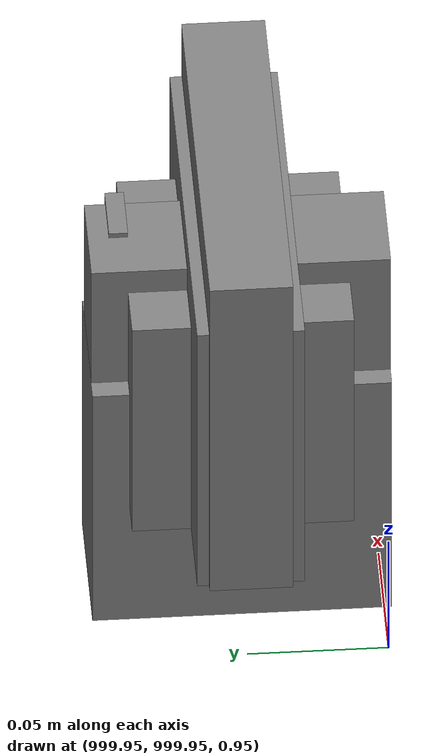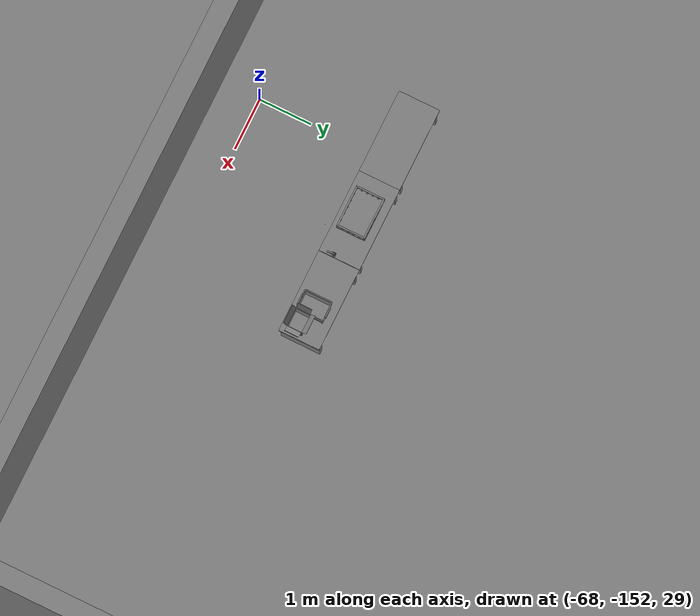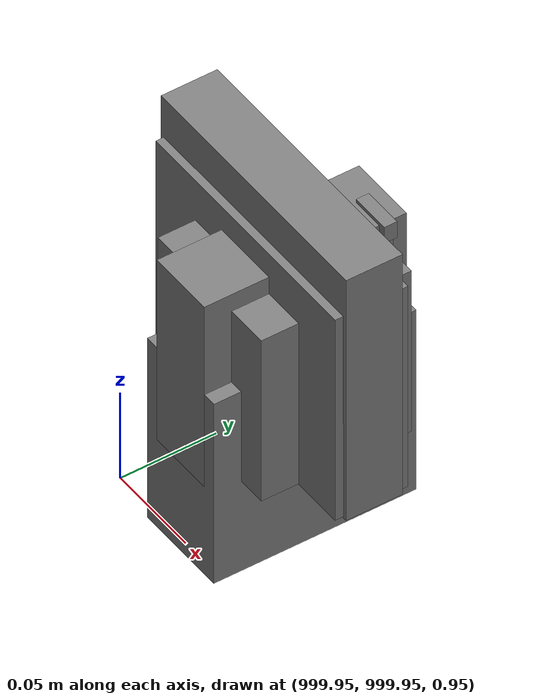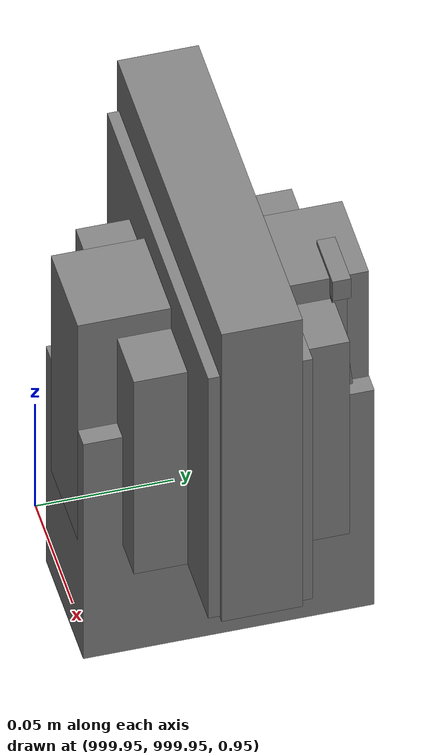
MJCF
<mujoco>
    <option gravity="0.000000000 0.000000000 -9.810000420" timestep="0.0049999999" integrator="implicitfast" density="1.225" viscosity="1.8000001e-05" noslip_iterations="10" iterations="100" sdf_iterations="50">
        <flag multiccd="disable"/>
    </option>
    <size memory="1000M"/>
    <compiler coordinate="local"/>
    <worldbody>
        <light cutoff="30" pos="0 1 1" dir="0 -1 -2"/>
        <light cutoff="30" pos="0 -1 1" dir="0 1 -2"/>
        <body pos="-64.866622925 -149.383972168 30.183746338" euler="89.999984741 89.999946594 0.000000000" name="openloong_gripper_2f85_fix_base_usda_bluebox_01">
            <geom contype="1" conaffinity="1" density="1000" type="box" material="" rgba="0.500000000 0.500000000 0.500000000 1.000000000" solimp="0.899999976 0.949999988 0.001000000" friction="1.000000000 0.005000000 0.000100000" solref="0.020000000 1.000000000" margin="0" condim="3" group="0" pos="0.276580811 0.187225342 0.000068665" quat="0.707106948 0.000077471 0.707106352 0.000077486" size="0.100000001 0.057999998 0.010000000" name="openloong_gripper_2f85_fix_base_usda_geom_85818CE5_DEFB_4EA5_A4FB_2F72F0BA48A5"/>
            <geom contype="1" conaffinity="1" density="1000" type="box" material="" rgba="0.500000000 0.500000000 0.500000000 1.000000000" solimp="0.899999976 0.949999988 0.001000000" friction="1.000000000 0.005000000 0.000100000" solref="0.020000000 1.000000000" margin="0" condim="3" group="0" pos="0.000000000 0.002883911 0.000000000" quat="0.999999881 0.000000000 0.000000000 0.000000000" size="0.254000008 0.003000000 0.172000006" name="openloong_gripper_2f85_fix_base_usda_geom_41874C26_9697_4C3C_855E_953E4631B327"/>
            <geom contype="1" conaffinity="1" density="1000" type="box" material="" rgba="0.500000000 0.500000000 0.500000000 1.000000000" solimp="0.899999976 0.949999988 0.001000000" friction="1.000000000 0.005000000 0.000100000" solref="0.020000000 1.000000000" margin="0" condim="3" group="0" pos="0.000000000 0.124874115 0.173484802" quat="0.999796331 0.020176515 -0.000000015 0.000000030" size="0.259999990 0.119999997 0.007000000" name="openloong_gripper_2f85_fix_base_usda_geom_17DC55E7_9D55_4117_80F8_2923F3931E77"/>
            <geom contype="1" conaffinity="1" density="1000" type="box" material="" rgba="0.500000000 0.500000000 0.500000000 1.000000000" solimp="0.899999976 0.949999988 0.001000000" friction="1.000000000 0.005000000 0.000100000" solref="0.020000000 1.000000000" margin="0" condim="3" group="0" pos="0.000000000 0.124874115 -0.173469543" quat="0.999796331 -0.020176545 -0.000000015 0.000000000" size="0.259999990 0.119999997 0.007000000" name="openloong_gripper_2f85_fix_base_usda_geom_9E2CE4B6_13E3_4058_839A_DD609DA53693"/>
            <geom contype="1" conaffinity="1" density="1000" type="box" material="" rgba="0.500000000 0.500000000 0.500000000 1.000000000" solimp="0.899999976 0.949999988 0.001000000" friction="1.000000000 0.005000000 0.000100000" solref="0.020000000 1.000000000" margin="0" condim="3" group="0" pos="0.000000000 0.214008331 0.188980103" quat="0.999912977 0.013176724 0.000000015 0.000000000" size="0.259999990 0.029999999 0.012500000" name="openloong_gripper_2f85_fix_base_usda_geom_DDC2C60A_081D_4C9B_BC1D_033508A413A9"/>
            <geom contype="1" conaffinity="1" density="1000" type="box" material="" rgba="0.500000000 0.500000000 0.500000000 1.000000000" solimp="0.899999976 0.949999988 0.001000000" friction="1.000000000 0.005000000 0.000100000" solref="0.020000000 1.000000000" margin="0" condim="3" group="0" pos="-0.258361816 0.125289917 0.001876831" quat="0.702796936 -0.020792112 0.710783124 0.020769298" size="0.189999998 0.119999997 0.009000000" name="openloong_gripper_2f85_fix_base_usda_geom_CB7E8BB9_03E1_41B0_A071_A17BA6A98A79"/>
            <geom contype="1" conaffinity="1" density="1000" type="box" material="" rgba="0.500000000 0.500000000 0.500000000 1.000000000" solimp="0.899999976 0.949999988 0.001000000" friction="1.000000000 0.005000000 0.000100000" solref="0.020000000 1.000000000" margin="0" condim="3" group="0" pos="0.000000000 0.214008331 -0.188980103" quat="0.999912977 -0.013176769 0.000000030 0.000000015" size="0.259999990 0.029999999 0.012500000" name="openloong_gripper_2f85_fix_base_usda_geom_89ABC2D5_B3CF_4FBB_908B_BA911D84DDA1"/>
            <geom contype="1" conaffinity="1" density="1000" type="box" material="" rgba="0.500000000 0.500000000 0.500000000 1.000000000" solimp="0.899999976 0.949999988 0.001000000" friction="1.000000000 0.005000000 0.000100000" solref="0.020000000 1.000000000" margin="0" condim="3" group="0" pos="-0.276611328 0.187225342 0.000068665" quat="0.707106650 0.000077441 0.707106709 0.000077456" size="0.100000001 0.057999998 0.010000000" name="openloong_gripper_2f85_fix_base_usda_geom_B4598F8A_2E9C_4ED6_AE52_7962EDCA9D59"/>
            <geom contype="1" conaffinity="1" density="1000" type="box" material="" rgba="0.500000000 0.500000000 0.500000000 1.000000000" solimp="0.899999976 0.949999988 0.001000000" friction="1.000000000 0.005000000 0.000100000" solref="0.020000000 1.000000000" margin="0" condim="3" group="0" pos="0.258331299 0.125289917 0.001876831" quat="0.702851415 0.018856421 0.710823774 -0.019329369" size="0.189999998 0.119999997 0.009000000" name="openloong_gripper_2f85_fix_base_usda_geom_5C47E67E_A911_4386_8F7C_3AE78965F368"/>
            <freejoint name="openloong_gripper_2f85_fix_base_usda_bluebox_01_joint"/>
            <site size="0.005000000 0.005000000 0.005000000" rgba="0.500000000 0.500000000 0.500000000 1.000000000" pos="0.000000000 0.000000000 0.000000000" quat="0.999961913 0.008726534 0.000000000 0.000000000" group="0" type="sphere" name="openloong_gripper_2f85_fix_base_usda_bluebox_01site"/>
        </body>
        <body pos="-64.496299744 -149.491867065 30.235729218" euler="0.000000000 0.000000000 89.999946594" name="openloong_gripper_2f85_fix_base_usda_cardboardbox_01">
            <geom contype="1" conaffinity="1" density="1000" type="box" material="" rgba="0.500000000 0.500000000 0.500000000 1.000000000" solimp="0.899999976 0.949999988 0.001000000" friction="1.000000000 0.005000000 0.000100000" solref="0.020000000 1.000000000" margin="0" condim="3" group="0" pos="-0.003166199 -0.004086494 0.005052090" quat="1.000000000 0.000000000 0.000000000 0.000000000" size="0.142499998 0.177500010 0.005000000" name="openloong_gripper_2f85_fix_base_usda_geom_B426BABB_9697_4476_BB4B_FCE8A878C2A7"/>
            <geom contype="1" conaffinity="1" density="1000" type="box" material="" rgba="0.500000000 0.500000000 0.500000000 1.000000000" solimp="0.899999976 0.949999988 0.001000000" friction="1.000000000 0.005000000 0.000100000" solref="0.020000000 1.000000000" margin="0" condim="3" group="0" pos="-0.003166199 0.170316696 0.150570869" quat="1.000000000 0.000000000 0.000000000 0.000000000" size="0.142499998 0.005000000 0.149999991" name="openloong_gripper_2f85_fix_base_usda_geom_BB726631_D220_4349_9153_B829CFE408D0"/>
            <geom contype="1" conaffinity="1" density="1000" type="box" material="" rgba="0.500000000 0.500000000 0.500000000 1.000000000" solimp="0.899999976 0.949999988 0.001000000" friction="1.000000000 0.005000000 0.000100000" solref="0.020000000 1.000000000" margin="0" condim="3" group="0" pos="-0.147399902 -0.005307198 0.150570869" quat="1.000000000 0.000000000 0.000000000 0.000000000" size="0.005000000 0.177500010 0.149999991" name="openloong_gripper_2f85_fix_base_usda_geom_CB0285EE_F088_49CE_936E_D48A60C28EB0"/>
            <geom contype="1" conaffinity="1" density="1000" type="box" material="" rgba="0.500000000 0.500000000 0.500000000 1.000000000" solimp="0.899999976 0.949999988 0.001000000" friction="1.000000000 0.005000000 0.000100000" solref="0.020000000 1.000000000" margin="0" condim="3" group="0" pos="0.140275955 -0.005307198 0.150570869" quat="1.000000000 0.000000000 0.000000000 0.000000000" size="0.005000000 0.177500010 0.149999991" name="openloong_gripper_2f85_fix_base_usda_geom_EF88679E_D903_48E3_9B2C_3FD9BD93E686"/>
            <geom contype="1" conaffinity="1" density="1000" type="box" material="" rgba="0.500000000 0.500000000 0.500000000 1.000000000" solimp="0.899999976 0.949999988 0.001000000" friction="1.000000000 0.005000000 0.000100000" solref="0.020000000 1.000000000" margin="0" condim="3" group="0" pos="-0.003166199 -0.181550980 0.150570869" quat="1.000000000 0.000000000 0.000000000 0.000000000" size="0.142499998 0.005000000 0.149999991" name="openloong_gripper_2f85_fix_base_usda_geom_AAB4730D_FEB1_45FF_B4D7_004CDF4457FD"/>
            <freejoint name="openloong_gripper_2f85_fix_base_usda_cardboardbox_01_joint"/>
            <site size="0.005000000 0.005000000 0.005000000" rgba="0.500000000 0.500000000 0.500000000 1.000000000" pos="0.000000000 0.000000000 0.000000000" quat="0.999961913 0.008726535 0.000000000 0.000000000" group="0" type="sphere" name="openloong_gripper_2f85_fix_base_usda_site_9EAE9806_389D_4F3F_A740_852F4FAB3D3A"/>
            <body pos="0.139160156 -0.004048347 0.301930904" euler="-179.999954224 49.383502960 179.999954224" name="openloong_gripper_2f85_fix_base_usda_A1_006">
                <geom contype="1" conaffinity="1" density="1000" type="box" material="" rgba="0.500000000 0.500000000 0.500000000 1.000000000" solimp="0.899999976 0.949999988 0.001000000" friction="1.000000000 0.005000000 0.000100000" solref="0.020000000 1.000000000" margin="0" condim="3" group="0" pos="-0.071587563 0.000009537 0.001745224" quat="0.999999881 0.000000000 0.000000000 0.000000000" size="0.071249999 0.179999992 0.002500000" name="openloong_gripper_2f85_fix_base_usda_geom_66D0C273_3DA5_4630_90B3_5551D4F7E062"/>
                <joint armature="0" stiffness="0.07" damping="0.0099999998" axis="0.000000 1.000000 0.000000" type="hinge" name="openloong_gripper_2f85_fix_base_usda_A1_006"/>
            </body>
            <body pos="-0.145902634 -0.004086494 0.301938057" euler="-180.000000000 -60.000011444 -180.000000000" name="openloong_gripper_2f85_fix_base_usda_A2_006">
                <geom contype="1" conaffinity="1" density="1000" type="box" material="" rgba="0.500000000 0.500000000 0.500000000 1.000000000" solimp="0.899999976 0.949999988 0.001000000" friction="1.000000000 0.005000000 0.000100000" solref="0.020000000 1.000000000" margin="0" condim="3" group="0" pos="0.071268082 0.000009537 0.002717972" quat="0.000002921 0.000000000 -0.000000030 0.999999881" size="0.071249999 0.179999992 0.002500000" name="openloong_gripper_2f85_fix_base_usda_geom_AD0ADF7C_9DB8_4165_9737_732634D1DEDD"/>
                <joint armature="0" stiffness="0.07" damping="0.0099999998" axis="0.000000 1.000000 0.000000" type="hinge" name="openloong_gripper_2f85_fix_base_usda_A2_006"/>
            </body>
            <body pos="-0.003385544 0.175991058 0.301930904" euler="-125.858116150 -0.000004561 0.000002331" name="openloong_gripper_2f85_fix_base_usda_B2_006">
                <geom contype="1" conaffinity="1" density="1000" type="box" material="" rgba="0.500000000 0.500000000 0.500000000 1.000000000" solimp="0.899999976 0.949999988 0.001000000" friction="1.000000000 0.005000000 0.000100000" solref="0.020000000 1.000000000" margin="0" condim="3" group="0" pos="0.000009537 -0.070939064 -0.002470016" quat="0.999614120 0.027776197 -0.000000015 0.000000030" size="0.137500003 0.064999998 0.005000000" name="openloong_gripper_2f85_fix_base_usda_geom_5975D205_7936_4AD2_85D9_E7C714171014"/>
                <joint armature="0" stiffness="0.07" damping="0.0099999998" axis="1.000000 0.000000 0.000000" type="hinge" name="openloong_gripper_2f85_fix_base_usda_B2_006"/>
            </body>
            <body pos="-0.003385544 -0.184140205 0.301938057" euler="147.805557251 0.000000000 0.000000000" name="openloong_gripper_2f85_fix_base_usda_B1_006">
                <geom contype="1" conaffinity="1" density="1000" type="box" material="" rgba="0.500000000 0.500000000 0.500000000 1.000000000" solimp="0.899999976 0.949999988 0.001000000" friction="1.000000000 0.005000000 0.000100000" solref="0.020000000 1.000000000" margin="0" condim="3" group="0" pos="-0.000028610 0.070202351 -0.002703667" quat="0.999614179 -0.027776167 0.000000000 0.000000000" size="0.137500003 0.064999998 0.005000000" name="openloong_gripper_2f85_fix_base_usda_geom_03971E52_DECF_45E9_8FD8_3683100AABDF"/>
                <joint armature="0" stiffness="0.07" damping="0.0099999998" axis="1.000000 0.000000 0.000000" type="hinge" name="openloong_gripper_2f85_fix_base_usda_B1_006"/>
            </body>
        </body>
        <body pos="-65.882858276 -149.481979370 30.229999542" euler="-64.487716675 0.000000000 0.000000000" name="openloong_gripper_2f85_fix_base_usda_Barcode">
            <geom contype="1" conaffinity="1" density="1000" type="box" material="" rgba="0.500000000 0.500000000 0.500000000 1.000000000" solimp="0.899999976 0.949999988 0.001000000" friction="1.000000000 0.005000000 0.000100000" solref="0.020000000 1.000000000" margin="0" condim="3" group="0" pos="0.000000000 0.013038635 0.001419067" quat="0.000000000 0.000000000 0.000000000 1.000000119" size="0.034000002 0.010000000 0.017999999" name="openloong_gripper_2f85_fix_base_usda_geom_0F11DACC_1971_43BF_A28D_CE4011B15846"/>
            <geom contype="1" conaffinity="1" density="1000" type="box" material="" rgba="0.500000000 0.500000000 0.500000000 1.000000000" solimp="0.899999976 0.949999988 0.001000000" friction="1.000000000 0.005000000 0.000100000" solref="0.020000000 1.000000000" margin="0" condim="3" group="0" pos="0.000000000 -0.035301208 -0.007095337" quat="0.000000000 0.000000000 -0.043619365 0.999048233" size="0.028999999 0.010000000 0.020000000" name="openloong_gripper_2f85_fix_base_usda_geom_720631CD_6BC3_4992_A377_01797C5D8280"/>
            <geom contype="1" conaffinity="1" density="1000" type="box" material="" rgba="0.500000000 0.500000000 0.500000000 1.000000000" solimp="0.899999976 0.949999988 0.001000000" friction="1.000000000 0.005000000 0.000100000" solref="0.020000000 1.000000000" margin="0" condim="3" group="0" pos="0.000000000 -0.043411255 -0.011749268" quat="0.922262907 0.386563420 0.000000000 0.000000000" size="0.026000001 0.010000000 0.020000000" name="openloong_gripper_2f85_fix_base_usda_geom_2E285DEE_2664_4BAE_BAE4_D9D71B28CCF0"/>
            <geom contype="1" conaffinity="1" density="1000" type="box" material="" rgba="0.500000000 0.500000000 0.500000000 1.000000000" solimp="0.899999976 0.949999988 0.001000000" friction="1.000000000 0.005000000 0.000100000" solref="0.020000000 1.000000000" margin="0" condim="3" group="0" pos="0.000000000 -0.016967773 -0.031860352" quat="0.000000000 0.000000000 0.000000000 1.000000119" size="0.008000000 0.010000000 0.013000000" name="openloong_gripper_2f85_fix_base_usda_geom_7103A8EE_FA31_4612_8570_0ECA7FE850FB"/>
            <geom contype="1" conaffinity="1" density="1000" type="box" material="" rgba="0.500000000 0.500000000 0.500000000 1.000000000" solimp="0.899999976 0.949999988 0.001000000" friction="1.000000000 0.005000000 0.000100000" solref="0.020000000 1.000000000" margin="0" condim="3" group="0" pos="0.000000000 -0.001869202 0.000312805" quat="0.953716993 0.300705761 0.000000000 0.000000000" size="0.032000002 0.010000000 0.018999999" name="openloong_gripper_2f85_fix_base_usda_geom_84A12C46_157E_47BF_8F25_47891EADCE48"/>
            <geom contype="1" conaffinity="1" density="1000" type="box" material="" rgba="0.500000000 0.500000000 0.500000000 1.000000000" solimp="0.899999976 0.949999988 0.001000000" friction="1.000000000 0.005000000 0.000100000" solref="0.020000000 1.000000000" margin="0" condim="3" group="0" pos="0.000000000 -0.019531250 -0.003173828" quat="0.953716993 0.300705761 0.000000000 0.000000000" size="0.030999999 0.010000000 0.020000000" name="openloong_gripper_2f85_fix_base_usda_geom_638B046D_52C7_4A60_AB13_12632018D560"/>
            <geom contype="1" conaffinity="1" density="1000" type="box" material="" rgba="0.500000000 0.500000000 0.500000000 1.000000000" solimp="0.899999976 0.949999988 0.001000000" friction="1.000000000 0.005000000 0.000100000" solref="0.020000000 1.000000000" margin="0" condim="3" group="0" pos="0.000000000 -0.035301208 -0.007095337" quat="0.953716993 0.300705761 0.000000000 0.000000000" size="0.028999999 0.010000000 0.020000000" name="openloong_gripper_2f85_fix_base_usda_geom_0B601370_2106_4856_8500_8366A762C2CC"/>
            <geom contype="1" conaffinity="1" density="1000" type="box" material="" rgba="0.500000000 0.500000000 0.500000000 1.000000000" solimp="0.899999976 0.949999988 0.001000000" friction="1.000000000 0.005000000 0.000100000" solref="0.020000000 1.000000000" margin="0" condim="3" group="0" pos="0.000000000 -0.042617798 -0.071121216" quat="0.000000000 0.000000000 0.000000000 1.000000119" size="0.013000000 0.021000000 0.059999999" name="openloong_gripper_2f85_fix_base_usda_geom_24FE02E9_DFA0_402E_AF46_D134CDE82E8E"/>
            <freejoint name="openloong_gripper_2f85_fix_base_usda_Barcode_joint"/>
            <site size="0.005000000 0.005000000 0.005000000" rgba="0.500000000 0.500000000 0.500000000 1.000000000" pos="0.000000000 0.000000000 0.000000000" quat="1.000000000 0.000000000 0.000000000 0.000000000" group="0" type="sphere" name="openloong_gripper_2f85_fix_base_usda_Barcode_site"/>
        </body>
        <body pos="-66.745018005 -149.392349243 30.184000015" euler="0.000000000 0.000000000 89.999946594" name="[22331803820515]_Basket_01">
            <geom contype="1" conaffinity="1" density="1000" type="box" material="" rgba="0.500000000 0.500000000 0.500000000 1.000000000" solimp="0.899999976 0.949999988 0.001000000" friction="1.000000000 0.005000000 0.000100000" solref="0.020000000 1.000000000" margin="0" condim="3" group="0" pos="-0.052425385 0.389207840 0.089787483" quat="0.707107008 0.000000000 0.000000000 0.707106411" size="0.014249999 0.014249999 0.059999999" name="[22331803820515]_geom_5D168D59_A18B_43B0_BC93_F92284AC3771"/>
            <geom contype="1" conaffinity="1" density="1000" type="box" material="" rgba="0.500000000 0.500000000 0.500000000 1.000000000" solimp="0.899999976 0.949999988 0.001000000" friction="1.000000000 0.005000000 0.000100000" solref="0.020000000 1.000000000" margin="0" condim="3" group="0" pos="0.264015198 -0.133043289 0.089787483" quat="0.707107008 0.000000000 0.000000000 0.707106411" size="0.014249999 0.014249999 0.059999999" name="[22331803820515]_geom_2084D36D_93F9_44C5_90BB_57EDBCA19D3E"/>
            <geom contype="1" conaffinity="1" density="1000" type="box" material="" rgba="0.500000000 0.500000000 0.500000000 1.000000000" solimp="0.899999976 0.949999988 0.001000000" friction="1.000000000 0.005000000 0.000100000" solref="0.020000000 1.000000000" margin="0" condim="3" group="0" pos="-0.264015198 -0.265548706 0.089793205" quat="0.707107008 0.000000000 0.000000000 0.707106411" size="0.014249999 0.014249999 0.059999999" name="[22331803820515]_geom_81C88AE8_518A_484D_B7D7_FE9AB8215944"/>
            <geom contype="1" conaffinity="1" density="1000" type="box" material="" rgba="0.500000000 0.500000000 0.500000000 1.000000000" solimp="0.899999976 0.949999988 0.001000000" friction="1.000000000 0.005000000 0.000100000" solref="0.020000000 1.000000000" margin="0" condim="3" group="0" pos="-0.160263062 -0.389322281 0.089793205" quat="0.707107008 0.000000000 0.000000000 0.707106411" size="0.014249999 0.014249999 0.059999999" name="[22331803820515]_geom_08CAD449_4F24_4E38_BC69_E7597E30FF76"/>
            <geom contype="1" conaffinity="1" density="1000" type="box" material="" rgba="0.500000000 0.500000000 0.500000000 1.000000000" solimp="0.899999976 0.949999988 0.001000000" friction="1.000000000 0.005000000 0.000100000" solref="0.020000000 1.000000000" margin="0" condim="3" group="0" pos="0.162265778 -0.389322281 0.089787483" quat="0.707107008 0.000000000 0.000000000 0.707106411" size="0.014249999 0.014249999 0.059999999" name="[22331803820515]_geom_DF8C5C83_EFB5_439C_8B20_0722C1A48D96"/>
            <geom contype="1" conaffinity="1" density="1000" type="box" material="" rgba="0.500000000 0.500000000 0.500000000 1.000000000" solimp="0.899999976 0.949999988 0.001000000" friction="1.000000000 0.005000000 0.000100000" solref="0.020000000 1.000000000" margin="0" condim="3" group="0" pos="0.264015198 0.389207840 0.089787483" quat="0.707107008 0.000000000 0.000000000 0.707106411" size="0.014249999 0.014249999 0.059999999" name="[22331803820515]_geom_EC075F77_D50A_4831_BA5E_ACBDFDB1F09B"/>
            <geom contype="1" conaffinity="1" density="1000" type="box" material="" rgba="0.500000000 0.500000000 0.500000000 1.000000000" solimp="0.899999976 0.949999988 0.001000000" friction="1.000000000 0.005000000 0.000100000" solref="0.020000000 1.000000000" margin="0" condim="3" group="0" pos="-0.264015198 -0.133043289 0.089793205" quat="0.707107008 0.000000000 0.000000000 0.707106411" size="0.014249999 0.014249999 0.059999999" name="[22331803820515]_geom_7AECA1D4_C89D_44D7_8158_DDA741FFC36E"/>
            <geom contype="1" conaffinity="1" density="1000" type="box" material="" rgba="0.500000000 0.500000000 0.500000000 1.000000000" solimp="0.899999976 0.949999988 0.001000000" friction="1.000000000 0.005000000 0.000100000" solref="0.020000000 1.000000000" margin="0" condim="3" group="0" pos="-0.264026642 0.269256592 0.089793205" quat="0.707107008 0.000000000 0.000000000 0.707106411" size="0.014249999 0.014249999 0.059999999" name="[22331803820515]_geom_B2E94109_95BE_4A24_8CB7_7541E1F84CE8"/>
            <geom contype="1" conaffinity="1" density="1000" type="box" material="" rgba="0.500000000 0.500000000 0.500000000 1.000000000" solimp="0.899999976 0.949999988 0.001000000" friction="1.000000000 0.005000000 0.000100000" solref="0.020000000 1.000000000" margin="0" condim="3" group="0" pos="0.054462433 0.389207840 0.089787483" quat="0.707107008 0.000000000 0.000000000 0.707106411" size="0.014249999 0.014249999 0.059999999" name="[22331803820515]_geom_CEE4FED6_841A_4A8D_9D5B_CAF26DA66DB9"/>
            <geom contype="1" conaffinity="1" density="1000" type="box" material="" rgba="0.500000000 0.500000000 0.500000000 1.000000000" solimp="0.899999976 0.949999988 0.001000000" friction="1.000000000 0.005000000 0.000100000" solref="0.020000000 1.000000000" margin="0" condim="3" group="0" pos="0.054462433 -0.389322281 0.089787483" quat="0.707107008 0.000000000 0.000000000 0.707106411" size="0.014249999 0.014249999 0.059999999" name="[22331803820515]_geom_94A84C9B_ECA8_4615_A842_DB8608E8F2C7"/>
            <geom contype="1" conaffinity="1" density="1000" type="box" material="" rgba="0.500000000 0.500000000 0.500000000 1.000000000" solimp="0.899999976 0.949999988 0.001000000" friction="1.000000000 0.005000000 0.000100000" solref="0.020000000 1.000000000" margin="0" condim="3" group="0" pos="0.264015198 0.269256592 0.089793205" quat="0.707107008 0.000000000 0.000000000 0.707106411" size="0.014249999 0.014249999 0.059999999" name="[22331803820515]_geom_80AE4061_07C4_408C_B73B_3C9CFCE928F4"/>
            <geom contype="1" conaffinity="1" density="1000" type="box" material="" rgba="0.500000000 0.500000000 0.500000000 1.000000000" solimp="0.899999976 0.949999988 0.001000000" friction="1.000000000 0.005000000 0.000100000" solref="0.020000000 1.000000000" margin="0" condim="3" group="0" pos="0.264015198 -0.389322281 0.089787483" quat="0.707107008 0.000000000 0.000000000 0.707106411" size="0.014249999 0.014249999 0.059999999" name="[22331803820515]_geom_D3706506_DEFB_40CC_A136_BB4E4900236C"/>
            <geom contype="1" conaffinity="1" density="1000" type="box" material="" rgba="0.500000000 0.500000000 0.500000000 1.000000000" solimp="0.899999976 0.949999988 0.001000000" friction="1.000000000 0.005000000 0.000100000" solref="0.020000000 1.000000000" margin="0" condim="3" group="0" pos="0.000000000 0.000000000 0.015998840" quat="0.707107008 0.000000000 0.000000000 0.707106411" size="0.403499991 0.279000014 0.015750000" name="[22331803820515]_geom_402896F4_3671_479F_86BA_3FE9CE2BBDB3"/>
            <geom contype="1" conaffinity="1" density="1000" type="box" material="" rgba="0.500000000 0.500000000 0.500000000 1.000000000" solimp="0.899999976 0.949999988 0.001000000" friction="1.000000000 0.005000000 0.000100000" solref="0.020000000 1.000000000" margin="0" condim="3" group="0" pos="0.000000000 -0.389476776 0.163619041" quat="0.707107008 0.000000000 0.000000000 0.707106411" size="0.015000000 0.277500004 0.015750000" name="[22331803820515]_geom_9106A630_E760_4833_88C4_5C9856573A39"/>
            <geom contype="1" conaffinity="1" density="1000" type="box" material="" rgba="0.500000000 0.500000000 0.500000000 1.000000000" solimp="0.899999976 0.949999988 0.001000000" friction="1.000000000 0.005000000 0.000100000" solref="0.020000000 1.000000000" margin="0" condim="3" group="0" pos="0.162265778 0.389207840 0.089787483" quat="0.707107008 0.000000000 0.000000000 0.707106411" size="0.014249999 0.014249999 0.059999999" name="[22331803820515]_geom_02A2DBF2_BE77_4AE3_8DE1_72114B3E6AF7"/>
            <geom contype="1" conaffinity="1" density="1000" type="box" material="" rgba="0.500000000 0.500000000 0.500000000 1.000000000" solimp="0.899999976 0.949999988 0.001000000" friction="1.000000000 0.005000000 0.000100000" solref="0.020000000 1.000000000" margin="0" condim="3" group="0" pos="0.000000000 0.389471054 0.163619041" quat="0.707107008 0.000000000 0.000000000 0.707106411" size="0.015000000 0.277500004 0.015750000" name="[22331803820515]_geom_C015A657_036C_4F1D_9CA3_E54BB9361A21"/>
            <geom contype="1" conaffinity="1" density="1000" type="box" material="" rgba="0.500000000 0.500000000 0.500000000 1.000000000" solimp="0.899999976 0.949999988 0.001000000" friction="1.000000000 0.005000000 0.000100000" solref="0.020000000 1.000000000" margin="0" condim="3" group="0" pos="-0.263511658 0.000000000 0.163619041" quat="0.707107008 0.000000000 0.000000000 0.707106411" size="0.403499991 0.015000000 0.015750000" name="[22331803820515]_geom_6E091884_3859_43C7_A2D8_924762E14042"/>
            <geom contype="1" conaffinity="1" density="1000" type="box" material="" rgba="0.500000000 0.500000000 0.500000000 1.000000000" solimp="0.899999976 0.949999988 0.001000000" friction="1.000000000 0.005000000 0.000100000" solref="0.020000000 1.000000000" margin="0" condim="3" group="0" pos="-0.264015198 0.141334534 0.089793205" quat="0.707107008 0.000000000 0.000000000 0.707106411" size="0.014249999 0.014249999 0.059999999" name="[22331803820515]_geom_0FBE7F11_530A_4260_A02A_81A9893C7833"/>
            <geom contype="1" conaffinity="1" density="1000" type="box" material="" rgba="0.500000000 0.500000000 0.500000000 1.000000000" solimp="0.899999976 0.949999988 0.001000000" friction="1.000000000 0.005000000 0.000100000" solref="0.020000000 1.000000000" margin="0" condim="3" group="0" pos="0.264015198 -0.265548706 0.089787483" quat="0.707107008 0.000000000 0.000000000 0.707106411" size="0.014249999 0.014249999 0.059999999" name="[22331803820515]_geom_89B01776_883D_4104_9CAE_2A3FB98650C5"/>
            <geom contype="1" conaffinity="1" density="1000" type="box" material="" rgba="0.500000000 0.500000000 0.500000000 1.000000000" solimp="0.899999976 0.949999988 0.001000000" friction="1.000000000 0.005000000 0.000100000" solref="0.020000000 1.000000000" margin="0" condim="3" group="0" pos="-0.160263062 0.389207840 0.089787483" quat="0.707107008 0.000000000 0.000000000 0.707106411" size="0.014249999 0.014249999 0.059999999" name="[22331803820515]_geom_5698FAD8_4BB6_41F3_BD84_EAFD995AF893"/>
            <geom contype="1" conaffinity="1" density="1000" type="box" material="" rgba="0.500000000 0.500000000 0.500000000 1.000000000" solimp="0.899999976 0.949999988 0.001000000" friction="1.000000000 0.005000000 0.000100000" solref="0.020000000 1.000000000" margin="0" condim="3" group="0" pos="-0.052425385 -0.389322281 0.089787483" quat="0.707107008 0.000000000 0.000000000 0.707106411" size="0.014249999 0.014249999 0.059999999" name="[22331803820515]_geom_C02037E1_1A56_4989_B5F1_21F5C79C1DAD"/>
            <geom contype="1" conaffinity="1" density="1000" type="box" material="" rgba="0.500000000 0.500000000 0.500000000 1.000000000" solimp="0.899999976 0.949999988 0.001000000" friction="1.000000000 0.005000000 0.000100000" solref="0.020000000 1.000000000" margin="0" condim="3" group="0" pos="-0.264026642 -0.389322281 0.089793205" quat="0.707107008 0.000000000 0.000000000 0.707106411" size="0.014249999 0.014249999 0.059999999" name="[22331803820515]_geom_3E5EB459_6760_4B5A_A0B7_5A31816E492B"/>
            <geom contype="1" conaffinity="1" density="1000" type="box" material="" rgba="0.500000000 0.500000000 0.500000000 1.000000000" solimp="0.899999976 0.949999988 0.001000000" friction="1.000000000 0.005000000 0.000100000" solref="0.020000000 1.000000000" margin="0" condim="3" group="0" pos="0.264015198 0.141334534 0.089787483" quat="0.707107008 0.000000000 0.000000000 0.707106411" size="0.014249999 0.014249999 0.059999999" name="[22331803820515]_geom_FAB77D9A_3F60_41F1_8E3D_0F9F6BAF3508"/>
            <geom contype="1" conaffinity="1" density="1000" type="box" material="" rgba="0.500000000 0.500000000 0.500000000 1.000000000" solimp="0.899999976 0.949999988 0.001000000" friction="1.000000000 0.005000000 0.000100000" solref="0.020000000 1.000000000" margin="0" condim="3" group="0" pos="-0.264015198 0.389207840 0.089793205" quat="0.707107008 0.000000000 0.000000000 0.707106411" size="0.014249999 0.014249999 0.059999999" name="[22331803820515]_geom_AAD635E2_8709_4F09_B2D6_EE9ABD2F02E5"/>
            <geom contype="1" conaffinity="1" density="1000" type="box" material="" rgba="0.500000000 0.500000000 0.500000000 1.000000000" solimp="0.899999976 0.949999988 0.001000000" friction="1.000000000 0.005000000 0.000100000" solref="0.020000000 1.000000000" margin="0" condim="3" group="0" pos="0.264015198 0.004480362 0.089787483" quat="0.707107008 0.000000000 0.000000000 0.707106411" size="0.014249999 0.014249999 0.059999999" name="[22331803820515]_geom_3ADD47E1_C25E_4105_9BF4_8C5EA882CD4C"/>
            <geom contype="1" conaffinity="1" density="1000" type="box" material="" rgba="0.500000000 0.500000000 0.500000000 1.000000000" solimp="0.899999976 0.949999988 0.001000000" friction="1.000000000 0.005000000 0.000100000" solref="0.020000000 1.000000000" margin="0" condim="3" group="0" pos="0.263694763 -0.000011444 0.163619041" quat="0.707107008 0.000000000 0.000000000 0.707106411" size="0.403499991 0.015000000 0.015750000" name="[22331803820515]_geom_80400DB2_A94D_46A7_8A0D_42FE891D60E1"/>
            <geom contype="1" conaffinity="1" density="1000" type="box" material="" rgba="0.500000000 0.500000000 0.500000000 1.000000000" solimp="0.899999976 0.949999988 0.001000000" friction="1.000000000 0.005000000 0.000100000" solref="0.020000000 1.000000000" margin="0" condim="3" group="0" pos="-0.264015198 0.004480362 0.089793205" quat="0.707107008 0.000000000 0.000000000 0.707106411" size="0.014249999 0.014249999 0.059999999" name="[22331803820515]_geom_185A876B_0C1C_4023_A89A_4D5EF96C841B"/>
            <freejoint name="[22331803820515]_joint_6E28C73B_B7AC_45F8_80EB_EAC7ACCC49EF"/>
        </body>
        <body pos="0.000000000 0.000000000 0.000000000" euler="0.000000000 0.000000000 0.000000000" name="Static Objects_Static Objects">
            <geom contype="1" conaffinity="1" density="1000" type="box" material="" rgba="0.500000000 0.500000000 0.500000000 1.000000000" solimp="0.899999976 0.949999988 0.001000000" friction="1.000000000 0.005000000 0.000100000" solref="0.020000000 1.000000000" margin="0" condim="3" group="0" pos="-67.544113159 -149.365814209 29.727830887" quat="0.500000417 0.499999970 0.499999553 0.499999970" size="0.381000012 0.319999993 0.041000001" name="Static Objects_geom_DD1BD6ED_2B0D_48D2_B6D7_9582D5C64B8B"/>
            <geom contype="1" conaffinity="1" density="1000" type="box" material="" rgba="0.500000000 0.500000000 0.500000000 1.000000000" solimp="0.899999976 0.949999988 0.001000000" friction="1.000000000 0.005000000 0.000100000" solref="0.020000000 1.000000000" margin="0" condim="3" group="0" pos="-68.239501953 -149.365814209 30.086868286" quat="0.500000417 0.499999970 0.499999553 0.499999970" size="0.370999992 0.039500002 0.745000005" name="Static Objects_geom_7A056469_022A_4152_B605_CD7DD0B38F66"/>
            <geom contype="1" conaffinity="1" density="1000" type="box" material="" rgba="0.500000000 0.500000000 0.500000000 1.000000000" solimp="0.899999976 0.949999988 0.001000000" friction="1.000000000 0.005000000 0.000100000" solref="0.020000000 1.000000000" margin="0" condim="3" group="0" pos="-68.239501953 -149.365814209 30.147235870" quat="0.500000417 0.499999970 0.499999553 0.499999970" size="0.400000006 0.022000000 0.800000012" name="Static Objects_geom_88B8B0EE_6F8D_41E8_89DF_3CD7FF9A526A"/>
            <geom contype="1" conaffinity="1" density="1000" type="box" material="" rgba="0.500000000 0.500000000 0.500000000 1.000000000" solimp="0.899999976 0.949999988 0.001000000" friction="1.000000000 0.005000000 0.000100000" solref="0.020000000 1.000000000" margin="0" condim="3" group="0" pos="-68.934890747 -149.365814209 29.727830887" quat="0.500000417 0.499999970 0.499999553 0.499999970" size="0.381000012 0.319999993 0.041000001" name="Static Objects_geom_BFD564BB_DE4A_4E5F_8377_B871683FDABD"/>
            <geom contype="1" conaffinity="1" density="1000" type="box" material="" rgba="0.500000000 0.500000000 0.500000000 1.000000000" solimp="0.899999976 0.949999988 0.001000000" friction="1.000000000 0.005000000 0.000100000" solref="0.020000000 1.000000000" margin="0" condim="3" group="0" pos="-68.239501953 -149.365814209 29.561563492" quat="0.500000417 0.499999970 0.499999553 0.499999970" size="0.020000000 0.022000000 0.660000026" name="Static Objects_geom_3433D1D2_5A6D_4F79_9399_E4800E777951"/>
            <geom contype="1" conaffinity="1" density="1000" type="box" material="" rgba="0.500000000 0.500000000 0.500000000 1.000000000" solimp="0.899999976 0.949999988 0.001000000" friction="1.000000000 0.005000000 0.000100000" solref="0.020000000 1.000000000" margin="0" condim="3" group="0" pos="-65.945671082 -149.365814209 29.727830887" quat="0.500000417 0.499999970 0.499999553 0.499999970" size="0.381000012 0.319999993 0.041000001" name="Static Objects_geom_BA2C2068_FB2D_45BB_9568_D51235ED9B0B"/>
            <geom contype="1" conaffinity="1" density="1000" type="box" material="" rgba="0.500000000 0.500000000 0.500000000 1.000000000" solimp="0.899999976 0.949999988 0.001000000" friction="1.000000000 0.005000000 0.000100000" solref="0.020000000 1.000000000" margin="0" condim="3" group="0" pos="-66.641059875 -149.365814209 30.086868286" quat="0.500000417 0.499999970 0.499999553 0.499999970" size="0.370999992 0.039500002 0.745000005" name="Static Objects_geom_B5091299_E28C_41FB_BE29_C8B26FBBD3A2"/>
            <geom contype="1" conaffinity="1" density="1000" type="box" material="" rgba="0.500000000 0.500000000 0.500000000 1.000000000" solimp="0.899999976 0.949999988 0.001000000" friction="1.000000000 0.005000000 0.000100000" solref="0.020000000 1.000000000" margin="0" condim="3" group="0" pos="-66.641059875 -149.365814209 30.147235870" quat="0.500000417 0.499999970 0.499999553 0.499999970" size="0.400000006 0.022000000 0.800000012" name="Static Objects_geom_F5161CC4_611E_41CA_A5FF_DC9EEE2A84FB"/>
            <geom contype="1" conaffinity="1" density="1000" type="box" material="" rgba="0.500000000 0.500000000 0.500000000 1.000000000" solimp="0.899999976 0.949999988 0.001000000" friction="1.000000000 0.005000000 0.000100000" solref="0.020000000 1.000000000" margin="0" condim="3" group="0" pos="-67.336448669 -149.365814209 29.727830887" quat="0.500000417 0.499999970 0.499999553 0.499999970" size="0.381000012 0.319999993 0.041000001" name="Static Objects_geom_BA80A5A4_E51A_4EE7_BC7F_D83347E95196"/>
            <geom contype="1" conaffinity="1" density="1000" type="box" material="" rgba="0.500000000 0.500000000 0.500000000 1.000000000" solimp="0.899999976 0.949999988 0.001000000" friction="1.000000000 0.005000000 0.000100000" solref="0.020000000 1.000000000" margin="0" condim="3" group="0" pos="-66.641059875 -149.365814209 29.561563492" quat="0.500000417 0.499999970 0.499999553 0.499999970" size="0.020000000 0.022000000 0.660000026" name="Static Objects_geom_2FF15229_44A9_433C_9721_2FDDE4297D02"/>
            <geom contype="1" conaffinity="1" density="1000" type="box" material="" rgba="0.500000000 0.500000000 0.500000000 1.000000000" solimp="0.899999976 0.949999988 0.001000000" friction="1.000000000 0.005000000 0.000100000" solref="0.020000000 1.000000000" margin="0" condim="3" group="0" pos="-64.338577271 -149.365814209 29.727830887" quat="0.500000417 0.499999970 0.499999553 0.499999970" size="0.381000012 0.319999993 0.041000001" name="Static Objects_geom_0ACCF39A_3BE0_4100_9115_661EB67F606C"/>
            <geom contype="1" conaffinity="1" density="1000" type="box" material="" rgba="0.500000000 0.500000000 0.500000000 1.000000000" solimp="0.899999976 0.949999988 0.001000000" friction="1.000000000 0.005000000 0.000100000" solref="0.020000000 1.000000000" margin="0" condim="3" group="0" pos="-65.033966064 -149.365814209 30.086868286" quat="0.500000417 0.499999970 0.499999553 0.499999970" size="0.370999992 0.039500002 0.745000005" name="Static Objects_geom_FAB84FF2_5623_4389_A93D_D6A17A2FEB6B"/>
            <geom contype="1" conaffinity="1" density="1000" type="box" material="" rgba="0.500000000 0.500000000 0.500000000 1.000000000" solimp="0.899999976 0.949999988 0.001000000" friction="1.000000000 0.005000000 0.000100000" solref="0.020000000 1.000000000" margin="0" condim="3" group="0" pos="-65.033966064 -149.365814209 30.147235870" quat="0.500000417 0.499999970 0.499999553 0.499999970" size="0.400000006 0.022000000 0.800000012" name="Static Objects_geom_22A32282_66F1_4B4F_8935_79FA2822E87B"/>
            <geom contype="1" conaffinity="1" density="1000" type="box" material="" rgba="0.500000000 0.500000000 0.500000000 1.000000000" solimp="0.899999976 0.949999988 0.001000000" friction="1.000000000 0.005000000 0.000100000" solref="0.020000000 1.000000000" margin="0" condim="3" group="0" pos="-65.729354858 -149.365814209 29.727830887" quat="0.500000417 0.499999970 0.499999553 0.499999970" size="0.381000012 0.319999993 0.041000001" name="Static Objects_geom_FB697C6E_FB9A_4F9C_B470_7E371BD218A2"/>
            <geom contype="1" conaffinity="1" density="1000" type="box" material="" rgba="0.500000000 0.500000000 0.500000000 1.000000000" solimp="0.899999976 0.949999988 0.001000000" friction="1.000000000 0.005000000 0.000100000" solref="0.020000000 1.000000000" margin="0" condim="3" group="0" pos="-65.033966064 -149.365814209 29.561563492" quat="0.500000417 0.499999970 0.499999553 0.499999970" size="0.020000000 0.022000000 0.660000026" name="Static Objects_geom_D247587D_AA31_4B70_A6E1_AA46C473424C"/>
            <geom contype="1" conaffinity="1" density="1000" type="box" material="" rgba="0.500000000 0.500000000 0.500000000 1.000000000" solimp="0.899999976 0.949999988 0.001000000" friction="1.000000000 0.005000000 0.000100000" solref="0.020000000 1.000000000" margin="0" condim="3" group="0" pos="-61.754566193 -137.853729248 33.906845093" quat="0.707107067 0.000000000 0.000000000 0.707106471" size="0.759999990 0.759999990 4.500000000" name="Static Objects_geom_F5D72AD2_3D9A_431A_9D5A_8D1FFCB83FBD"/>
            <geom contype="1" conaffinity="1" density="1000" type="box" material="" rgba="0.500000000 0.500000000 0.500000000 1.000000000" solimp="0.899999976 0.949999988 0.001000000" friction="1.000000000 0.005000000 0.000100000" solref="0.020000000 1.000000000" margin="0" condim="3" group="0" pos="-57.511135101 -144.927108765 31.707921982" quat="1.000000000 0.000000000 0.000000000 0.000000000" size="0.200000003 8.000000000 2.299999952" name="Static Objects_geom_9C2F06EB_5EA5_4D8C_9F93_1FA285D4588E"/>
            <geom contype="1" conaffinity="1" density="1000" type="box" material="" rgba="0.500000000 0.500000000 0.500000000 1.000000000" solimp="0.899999976 0.949999988 0.001000000" friction="1.000000000 0.005000000 0.000100000" solref="0.020000000 1.000000000" margin="0" condim="3" group="0" pos="-80.517646790 -157.574050903 31.688196182" quat="0.707107067 0.000000000 0.000000000 0.707106471" size="0.600000024 0.600000024 2.299999952" name="Static Objects_geom_3D8F8D57_2E4A_4453_9244_F9788970B025"/>
            <geom contype="1" conaffinity="1" density="1000" type="box" material="" rgba="0.500000000 0.500000000 0.500000000 1.000000000" solimp="0.899999976 0.949999988 0.001000000" friction="1.000000000 0.005000000 0.000100000" solref="0.020000000 1.000000000" margin="0" condim="3" group="0" pos="-80.711044312 -147.414932251 31.666158676" quat="1.000000000 0.000000000 0.000000000 0.000000000" size="0.200000003 10.000000000 2.299999952" name="Static Objects_geom_2D257886_3943_4E61_BEA0_6FA9AC83003D"/>
            <geom contype="1" conaffinity="1" density="1000" type="box" material="" rgba="0.500000000 0.500000000 0.500000000 1.000000000" solimp="0.899999976 0.949999988 0.001000000" friction="1.000000000 0.005000000 0.000100000" solref="0.020000000 1.000000000" margin="0" condim="3" group="0" pos="-57.687217712 -137.434692383 31.688196182" quat="0.707107067 0.000000000 0.000000000 0.707106471" size="0.600000024 0.600000024 2.299999952" name="Static Objects_geom_7C12ECE0_1714_40A9_A4D2_49D877908353"/>
            <geom contype="1" conaffinity="1" density="1000" type="box" material="" rgba="0.500000000 0.500000000 0.500000000 1.000000000" solimp="0.899999976 0.949999988 0.001000000" friction="1.000000000 0.005000000 0.000100000" solref="0.020000000 1.000000000" margin="0" condim="3" group="0" pos="-69.537033081 -140.263229370 31.714921951" quat="0.707107067 0.000000000 0.000000000 0.707106471" size="0.759999990 4.500000000 2.299999952" name="Static Objects_geom_C5D3A3B1_D339_4A5F_9ABB_85031517D318"/>
            <geom contype="1" conaffinity="1" density="1000" type="box" material="" rgba="0.500000000 0.500000000 0.500000000 1.000000000" solimp="0.899999976 0.949999988 0.001000000" friction="1.000000000 0.005000000 0.000100000" solref="0.020000000 1.000000000" margin="0" condim="3" group="0" pos="-80.073638916 -137.853713989 33.906845093" quat="0.707107067 0.000000000 0.000000000 0.707106471" size="0.759999990 0.759999990 4.500000000" name="Static Objects_geom_6011A80B_2EEC_4693_ACF1_E3E8A4C80646"/>
            <geom contype="1" conaffinity="1" density="1000" type="box" material="" rgba="0.500000000 0.500000000 0.500000000 1.000000000" solimp="0.899999976 0.949999988 0.001000000" friction="1.000000000 0.005000000 0.000100000" solref="0.020000000 1.000000000" margin="0" condim="3" group="0" pos="-73.406707764 -155.734664917 31.707921982" quat="1.000000000 0.000000000 0.000000000 0.000000000" size="0.200000003 3.000000000 2.299999952" name="Static Objects_geom_6A42E331_68DD_4174_96FA_5DEF0B765B2E"/>
            <geom contype="1" conaffinity="1" density="1000" type="box" material="" rgba="0.500000000 0.500000000 0.500000000 1.000000000" solimp="0.899999976 0.949999988 0.001000000" friction="1.000000000 0.005000000 0.000100000" solref="0.020000000 1.000000000" margin="0" condim="3" group="0" pos="-68.497543335 -137.448257446 31.707921982" quat="0.707107067 0.000000000 0.000000000 0.707106471" size="0.200000003 14.000000000 2.299999952" name="Static Objects_geom_8E990B44_2868_49FC_97D2_223A69A78EAC"/>
            <geom contype="1" conaffinity="1" density="1000" type="cylinder" material="" rgba="0.500000000 0.500000000 0.500000000 1.000000000" solimp="0.899999976 0.949999988 0.001000000" friction="1.000000000 0.005000000 0.000100000" solref="0.020000000 1.000000000" margin="0" condim="3" group="0" pos="-68.868522644 -142.134506226 31.711090088" quat="0.707107067 0.000000000 0.000000000 0.707106471" size="0.509999990 2.299999952 1.000000000" name="Static Objects_geom_1290928B_6C5C_44BB_B33B_5B10AAB71A8B"/>
            <geom contype="1" conaffinity="1" density="1000" type="plane" material="" rgba="0.500000000 0.500000000 0.500000000 1.000000000" solimp="0.899999976 0.949999988 0.001000000" friction="1.000000000 0.005000000 0.000100000" solref="0.020000000 1.000000000" margin="0" condim="3" group="0" pos="-72.873703003 -147.131927490 29.409669876" quat="1.000000000 0.000000000 0.000000000 0.000000000" size="18.000000000 14.000000000 1.000000000" name="Static Objects_geom_4D4C4E03_BAA9_4DD3_A4C0_9A29EB6FA37C"/>
            <geom contype="1" conaffinity="1" density="1000" type="box" material="" rgba="0.500000000 0.500000000 0.500000000 1.000000000" solimp="0.899999976 0.949999988 0.001000000" friction="1.000000000 0.005000000 0.000100000" solref="0.020000000 1.000000000" margin="0" condim="3" group="0" pos="-79.943580627 -157.782272339 31.707921982" quat="0.707107067 0.000000000 0.000000000 0.707106471" size="0.200000003 7.000000000 2.299999952" name="Static Objects_geom_575B3699_49BA_46A0_B1FB_FFE51A2CC467"/>
            <geom contype="1" conaffinity="1" density="1000" type="box" material="" rgba="0.500000000 0.500000000 0.500000000 1.000000000" solimp="0.899999976 0.949999988 0.001000000" friction="1.000000000 0.005000000 0.000100000" solref="0.020000000 1.000000000" margin="0" condim="3" group="0" pos="-65.421028137 -152.903442383 31.707921982" quat="0.707107067 0.000000000 0.000000000 0.707106471" size="0.200000003 7.800000191 2.299999952" name="Static Objects_geom_B99FBE73_F93F_4500_9E26_B1B0EA54F530"/>
            <geom contype="1" conaffinity="1" density="1000" type="box" material="" rgba="0.500000000 0.500000000 0.500000000 1.000000000" solimp="0.899999976 0.949999988 0.001000000" friction="1.000000000 0.005000000 0.000100000" solref="0.020000000 1.000000000" margin="0" condim="3" group="0" pos="-74.776908875 -149.964416504 31.688196182" quat="1.000000000 0.000000000 0.000000000 0.000000000" size="0.600000024 0.409999996 2.299999952" name="Static Objects_geom_EE093F15_89E3_4691_8D55_707FD271DB37"/>
            <geom contype="1" conaffinity="1" density="1000" type="cylinder" material="" rgba="0.500000000 0.500000000 0.500000000 1.000000000" solimp="0.899999976 0.949999988 0.001000000" friction="1.000000000 0.005000000 0.000100000" solref="0.020000000 1.000000000" margin="0" condim="3" group="0" pos="-60.161884308 -142.134506226 31.711090088" quat="0.707107067 0.000000000 0.000000000 0.707106471" size="0.509999990 2.299999952 1.000000000" name="Static Objects_geom_0CB0A7F7_F9F6_458F_B231_57B0171D62E4"/>
            <geom contype="1" conaffinity="1" density="1000" type="cylinder" material="" rgba="0.500000000 0.500000000 0.500000000 1.000000000" solimp="0.899999976 0.949999988 0.001000000" friction="1.000000000 0.005000000 0.000100000" solref="0.020000000 1.000000000" margin="0" condim="3" group="0" pos="-75.382453918 -149.963455200 31.711090088" quat="0.707107067 0.000000000 0.000000000 0.707106471" size="0.409999996 2.299999952 1.000000000" name="Static Objects_geom_849E890C_8AA7_4263_AFEA_B1DB5684E3DF"/>
            <geom contype="1" conaffinity="1" density="1000" type="cylinder" material="" rgba="0.500000000 0.500000000 0.500000000 1.000000000" solimp="0.899999976 0.949999988 0.001000000" friction="1.000000000 0.005000000 0.000100000" solref="0.020000000 1.000000000" margin="0" condim="3" group="0" pos="-74.154960632 -149.963455200 31.711090088" quat="0.707107067 0.000000000 0.000000000 0.707106471" size="0.409999996 2.299999952 1.000000000" name="Static Objects_geom_00F702C0_BA39_4301_92C3_A82AF8ECE87D"/>
            <geom contype="1" conaffinity="1" density="1000" type="cylinder" material="" rgba="0.500000000 0.500000000 0.500000000 1.000000000" solimp="0.899999976 0.949999988 0.001000000" friction="1.000000000 0.005000000 0.000100000" solref="0.020000000 1.000000000" margin="0" condim="3" group="0" pos="-77.566612244 -142.134506226 31.711090088" quat="0.707107067 0.000000000 0.000000000 0.707106471" size="0.509999990 2.299999952 1.000000000" name="Static Objects_geom_0321FC16_5F79_4C8D_AD63_A2B1AE2D5CA3"/>
        </body>
        <body pos="1000.000000000 1000.000000000 1.000000000" euler="0.000000000 0.000000000 180.000000000" name="openloong_gripper_2f85_fix_base_usda_wifi_box">
            <geom contype="1" conaffinity="1" density="1000" type="box" material="" rgba="0.500000000 0.500000000 0.500000000 1.000000000" solimp="0.899999976 0.949999988 0.001000000" friction="1.000000000 0.005000000 0.000100000" solref="0.020000000 1.000000000" margin="0" condim="3" group="0" pos="0.000000000 0.000000000 0.058978677" quat="0.000000000 0.000000047 0.000000000 1.000000000" size="0.068499997 0.018999999 0.059000000" name="openloong_gripper_2f85_fix_base_usda_geom_1BD612E2_B693_4D6A_AAFD_CE7E602BC510"/>
            <freejoint name="openloong_gripper_2f85_fix_base_usda_wifi_box_joint"/>
            <site size="0.005000000 0.005000000 0.005000000" rgba="0.500000000 0.500000000 0.500000000 1.000000000" pos="0.000000000 0.000000000 0.000000000" quat="0.999961913 0.008726500 0.000000000 0.000000000" group="0" type="sphere" name="openloong_gripper_2f85_fix_base_usda_wifi_boxsite"/>
        </body>
        <body pos="-65.977462769 -149.627273560 31.165586472" euler="119.802711487 -87.807319641 136.131088257" mocap="true" name="spotlight5_SpotLight"/>
        <body pos="1000.000000000 999.999938965 1.000000000" euler="0.000000000 0.000000000 180.000000000" name="openloong_gripper_2f85_fix_base_usda_intelcore_i5">
            <geom contype="1" conaffinity="1" density="1000" type="box" material="" rgba="0.500000000 0.500000000 0.500000000 1.000000000" solimp="0.899999976 0.949999988 0.001000000" friction="1.000000000 0.005000000 0.000100000" solref="0.020000000 1.000000000" margin="0" condim="3" group="0" pos="0.000000000 0.000000000 0.051722717" quat="0.707106709 0.000000000 0.000000000 -0.707106769" size="0.052800000 0.018080002 0.052800000" name="openloong_gripper_2f85_fix_base_usda_geom_C13277A3_5B3C_4ADE_9280_F0CD0AE41556"/>
            <freejoint name="openloong_gripper_2f85_fix_base_usda_intelcore_i5_joint"/>
            <site size="0.005000000 0.005000000 0.005000000" rgba="0.500000000 0.500000000 0.500000000 1.000000000" pos="0.000000000 0.000000000 0.000000000" quat="0.999961913 0.008726534 0.000000000 0.000000000" group="0" type="sphere" name="openloong_gripper_2f85_fix_base_usda_intelcore_i5site"/>
        </body>
        <body pos="1000.000000000 1000.000000000 1.000000000" euler="0.000011953 0.000005123 -179.999984741" name="openloong_gripper_2f85_fix_base_usda_intel_box">
            <geom contype="1" conaffinity="1" density="1000" type="box" material="" rgba="0.500000000 0.500000000 0.500000000 1.000000000" solimp="0.899999976 0.949999988 0.001000000" friction="1.000000000 0.005000000 0.000100000" solref="0.020000000 1.000000000" margin="0" condim="3" group="0" pos="0.000000000 -0.000067139 0.000082284" quat="0.707106709 0.000000225 0.000000253 0.707106650" size="0.052800003 0.025300000 0.052800003" name="openloong_gripper_2f85_fix_base_usda_geom_CB693FAE_859E_497A_87D3_1F24209F66A9"/>
            <freejoint name="openloong_gripper_2f85_fix_base_usda_intel_box_joint"/>
            <site size="0.005000000 0.005000000 0.005000000" rgba="0.500000000 0.500000000 0.500000000 1.000000000" pos="0.000000000 0.000000000 0.000000000" quat="0.999961913 0.008726500 0.000000000 0.000000000" group="0" type="sphere" name="openloong_gripper_2f85_fix_base_usda_intel_boxsite"/>
        </body>
        <body pos="-65.961318970 -149.127502441 31.163635254" euler="-144.522857666 -63.954498291 -72.166030884" mocap="true" name="spotlight2_SpotLight"/>
        <body pos="1000.000000000 1000.000000000 1.000000000" euler="0.000000000 0.000000000 180.000000000" name="openloong_gripper_2f85_fix_base_usda_cpu_fan">
            <geom contype="1" conaffinity="1" density="1000" type="box" material="" rgba="0.500000000 0.500000000 0.500000000 1.000000000" solimp="0.899999976 0.949999988 0.001000000" friction="1.000000000 0.005000000 0.000100000" solref="0.020000000 1.000000000" margin="0" condim="3" group="0" pos="0.000000000 0.000000000 0.070034981" quat="0.000000000 0.000000000 0.000000000 1.000000000" size="0.070700005 0.014699999 0.070700005" name="openloong_gripper_2f85_fix_base_usda_geom_718F6E07_2800_4B67_89ED_BDB684A58EFC"/>
            <freejoint name="openloong_gripper_2f85_fix_base_usda_cpu_fan_joint"/>
            <site size="0.005000000 0.005000000 0.005000000" rgba="0.500000000 0.500000000 0.500000000 1.000000000" pos="0.000000000 0.000000000 0.000000000" quat="0.999961913 0.008726535 0.000000000 0.000000000" group="0" type="sphere" name="openloong_gripper_2f85_fix_base_usda_cpu_fancsite"/>
        </body>
        <body pos="-65.896217346 -149.492996216 31.171400070" euler="-7.741653442 -33.064189911 161.911560059" mocap="true" name="spotlight3_SpotLight"/>
        <body pos="1000.000000000 1000.000000000 1.000000000" euler="0.000000000 0.000000000 180.000000000" name="openloong_gripper_2f85_fix_base_usda_battery_01">
            <geom contype="1" conaffinity="1" density="1000" type="box" material="" rgba="0.500000000 0.500000000 0.500000000 1.000000000" solimp="0.899999976 0.949999988 0.001000000" friction="1.000000000 0.005000000 0.000100000" solref="0.020000000 1.000000000" margin="0" condim="3" group="0" pos="-0.011123657 -0.041940309 0.101691343" quat="1.000000000 0.000000000 0.000000000 0.000000000" size="0.010800000 0.003375000 0.004725000" name="openloong_gripper_2f85_fix_base_usda_geom_EEE9855F_6F20_4A4C_B7E0_1CA6416EAEDE"/>
            <geom contype="1" conaffinity="1" density="1000" type="box" material="" rgba="0.500000000 0.500000000 0.500000000 1.000000000" solimp="0.899999976 0.949999988 0.001000000" friction="1.000000000 0.005000000 0.000100000" solref="0.020000000 1.000000000" margin="0" condim="3" group="0" pos="-0.010876465 -0.044247437 0.047066893" quat="0.998702705 -0.050920475 0.000000000 0.000000000" size="0.009450001 0.002700000 0.024975000" name="openloong_gripper_2f85_fix_base_usda_geom_86EBC1DC_CFC8_4977_996E_9113939E0AA5"/>
            <geom contype="1" conaffinity="1" density="1000" type="box" material="" rgba="0.500000000 0.500000000 0.500000000 1.000000000" solimp="0.899999976 0.949999988 0.001000000" friction="1.000000000 0.005000000 0.000100000" solref="0.020000000 1.000000000" margin="0" condim="3" group="0" pos="-0.001235962 -0.000659180 0.047381196" quat="1.000000000 0.000000000 0.000000000 0.000000000" size="0.039420001 0.039150000 0.047250003" name="openloong_gripper_2f85_fix_base_usda_geom_82A93E4D_4F53_428E_8E36_42F4C214B4FA"/>
            <geom contype="1" conaffinity="1" density="1000" type="box" material="" rgba="0.500000000 0.500000000 0.500000000 1.000000000" solimp="0.899999976 0.949999988 0.001000000" friction="1.000000000 0.005000000 0.000100000" solref="0.020000000 1.000000000" margin="0" condim="3" group="0" pos="-0.010876465 -0.039138794 0.009851727" quat="1.000000000 0.000000000 0.000000000 0.000000000" size="0.009450001 0.010800000 0.013500000" name="openloong_gripper_2f85_fix_base_usda_geom_B273FA6F_833F_4446_96CE_0C2133503635"/>
            <geom contype="1" conaffinity="1" density="1000" type="box" material="" rgba="0.500000000 0.500000000 0.500000000 1.000000000" solimp="0.899999976 0.949999988 0.001000000" friction="1.000000000 0.005000000 0.000100000" solref="0.020000000 1.000000000" margin="0" condim="3" group="0" pos="-0.010876465 -0.041528322 0.071508206" quat="1.000000000 0.000000000 0.000000000 0.000000000" size="0.009450001 0.002700000 0.027000001" name="openloong_gripper_2f85_fix_base_usda_geom_93E42214_29B9_4CF9_947A_91800A8D2E3C"/>
            <freejoint name="openloong_gripper_2f85_fix_base_usda_battery_01_joint"/>
            <site size="0.005000000 0.005000000 0.005000000" rgba="0.500000000 0.500000000 0.500000000 1.000000000" pos="0.000000000 0.000000000 0.000000000" quat="0.999961913 0.008726500 0.000000000 0.000000000" group="0" type="sphere" name="openloong_gripper_2f85_fix_base_usda_battery_01site"/>
        </body>
        <body pos="-66.291030884 -149.869689941 29.018842697" euler="0.000000000 0.000000000 89.999946594" mocap="true" name="openloong_gripper_2f85_fix_base_usda_leftHandMocap"/>
        <body pos="-66.291030884 -149.869689941 29.018842697" euler="0.000000000 0.000000000 89.999946594" mocap="true" name="openloong_gripper_2f85_fix_base_usda_rightHandMocap"/>
        <body pos="-66.291030884 -149.869689941 30.218843460" euler="0.000000000 0.000000000 89.999946594" name="openloong_gripper_2f85_fix_base_usda_base_link">
            <geom contype="1" conaffinity="1" density="1000" type="mesh" material="" rgba="0.783999979 0.783999979 0.783999979 1.000000000" solimp="0.899999976 0.949999988 0.001000000" friction="1.000000000 0.005000000 0.000100000" solref="0.020000000 1.000000000" margin="0" condim="3" group="3" mesh="base_link" pos="0.000000000 0.000000000 0.000000000" quat="1.000000000 0.000000000 0.000000000 0.000000000" size="1.000000000 1.000000000 1.000000000" name="openloong_gripper_2f85_fix_base_usda__geom_7_DE5587E0_2465_4D25_B690_F52D5BCFFC92"/>
            <site size="0.005000000 0.005000000 0.005000000" rgba="0.500000000 0.500000000 0.500000000 1.000000000" pos="0.000000000 0.000000000 0.000000000" quat="1.000000000 0.000000000 0.000000000 0.000000000" group="0" type="sphere" name="openloong_gripper_2f85_fix_base_usda_imu"/>
            <inertial mass="22.447001" pos="-0.005664100 -0.001336700 0.238289997" diaginertia="0.374352545 0.277180195 0.220617250" quat="0.999247074 0.035235517 -0.015086859 0.006023135"/>
            <body pos="0.000000000 0.000000000 0.299997330" euler="0.000000000 0.000000000 0.000000000" name="openloong_gripper_2f85_fix_base_usda_dummy_body">
                <geom contype="1" conaffinity="1" density="1000" type="sphere" material="" rgba="0.783999979 0.783999979 0.783999979 1.000000000" solimp="0.899999976 0.949999988 0.001000000" friction="1.000000000 0.005000000 0.000100000" solref="0.020000000 1.000000000" margin="0" condim="3" group="3" pos="0.000000000 0.000000000 0.000000000" quat="1.000000000 0.000000000 0.000000000 0.000000000" size="0.010000000 0.000000000 0.000000000" name="openloong_gripper_2f85_fix_base_usda__geom_8_D3BF7D3E_CE1F_4F83_AC51_3135234BB733"/>
                <joint armature="0.0099999998" stiffness="0" damping="0.1" axis="0.000000 0.000000 1.000000" type="hinge" name="openloong_gripper_2f85_fix_base_usda_dummy_joint"/>
                <site size="0.010000000 0.005000000 0.005000000" rgba="0.500000000 0.500000000 0.500000000 1.000000000" pos="0.000000000 0.000000000 0.000000000" quat="1.000000000 0.000000000 0.000000000 0.000000000" group="3" type="sphere" name="openloong_gripper_2f85_fix_base_usda_dummy_site"/>
            </body>
            <body pos="0.009002686 0.000000000 0.406400681" euler="0.000000000 0.000000000 0.000000000" name="openloong_gripper_2f85_fix_base_usda_Link_head_yaw">
                <geom contype="1" conaffinity="1" density="1000" type="mesh" material="" rgba="0.783999979 0.783999979 0.783999979 1.000000000" solimp="0.899999976 0.949999988 0.001000000" friction="1.000000000 0.005000000 0.000100000" solref="0.020000000 1.000000000" margin="0" condim="3" group="3" mesh="Link_head_yaw" pos="0.000000000 0.000000000 0.000000000" quat="1.000000000 0.000000000 0.000000000 0.000000000" size="1.000000000 1.000000000 1.000000000" name="openloong_gripper_2f85_fix_base_usda__geom_10_91816C20_3FCF_4799_AAEA_2F69D059B290"/>
                <inertial mass="0.84249002" pos="0.000000000 -0.002081400 0.044801001" diaginertia="0.000700588 0.000629000 0.000553812" quat="0.706933022 -0.015675601 0.015677100 0.706933022"/>
                <body pos="0.000000000 -0.034599304 0.048500061" euler="0.000000000 0.000000000 0.000000000" name="openloong_gripper_2f85_fix_base_usda_Link_head_pitch">
                    <geom contype="1" conaffinity="1" density="1000" type="mesh" material="" rgba="0.783999979 0.783999979 0.783999979 1.000000000" solimp="0.899999976 0.949999988 0.001000000" friction="1.000000000 0.005000000 0.000100000" solref="0.020000000 1.000000000" margin="0" condim="3" group="3" mesh="Link_head_pitch" pos="0.000000000 0.000000000 0.000000000" quat="1.000000000 0.000000000 0.000000000 0.000000000" size="1.000000000 1.000000000 1.000000000" name="openloong_gripper_2f85_fix_base_usda__geom_12_F87A3FDC_D122_4B7F_BC2E_932A269AA501"/>
                    <inertial mass="1.3943" pos="0.020569000 0.033004001 0.125000000" diaginertia="0.006381400 0.006289940 0.004481460" quat="0.973390222 0.008406822 0.228157058 0.019624906"/>
                    <body pos="0.000000000 0.029998779 0.000000000" euler="0.000000000 0.000000000 0.000000000" name="openloong_gripper_2f85_fix_base_usda_neck_center_body">
                        <site size="0.010000000 0.005000000 0.005000000" rgba="0.500000000 0.500000000 0.500000000 1.000000000" pos="0.000000000 0.000000000 0.000000000" quat="1.000000000 0.000000000 0.000000000 0.000000000" group="3" type="sphere" name="openloong_gripper_2f85_fix_base_usda_neck_center_site"/>
                        <body pos="0.020004272 0.000000000 0.149999619" euler="-0.000002229 39.998176575 -90.000205994" name="openloong_gripper_2f85_fix_base_usda_camera_head">
                            <site size="0.010000000 0.005000000 0.005000000" rgba="0.500000000 0.500000000 0.500000000 1.000000000" pos="0.000000000 0.000000000 0.000000000" quat="1.000000000 0.000000000 0.000000000 0.000000000" group="3" type="sphere" name="openloong_gripper_2f85_fix_base_usda_camera_head_site"/>
                        </body>
                    </body>
                </body>
            </body>
            <body pos="0.003997803 -0.161598206 0.392200470" euler="0.000000000 0.000000000 0.000000000" name="openloong_gripper_2f85_fix_base_usda_Link_arm_r_01">
                <geom contype="1" conaffinity="1" density="1000" type="mesh" material="" rgba="0.783999979 0.783999979 0.783999979 1.000000000" solimp="0.899999976 0.949999988 0.001000000" friction="1.000000000 0.005000000 0.000100000" solref="0.020000000 1.000000000" margin="0" condim="3" group="3" mesh="Link_arm_r_01" pos="0.000000000 0.000000000 0.000000000" quat="1.000000000 0.000000000 0.000000000 0.000000000" size="1.000000000 1.000000000 1.000000000" name="openloong_gripper_2f85_fix_base_usda__geom_14_B221A3EE_7018_4724_926C_383901108EC3"/>
                <joint armature="0.0099999998" stiffness="0" damping="1" axis="0.000000 -1.000000 0.000000" limited="true" range="-170.000015259 170.000015259" type="hinge" name="openloong_gripper_2f85_fix_base_usda_J_arm_r_01"/>
                <inertial mass="0.75641" pos="0.004494600 -0.038293999 -0.000001874" diaginertia="0.000842990 0.000803050 0.000587120" quat="-0.000163502 0.707098067 0.000812463 0.707115054"/>
                <body pos="-0.041992188 -0.041000366 0.000000000" euler="0.000000000 0.000000000 0.000000000" name="openloong_gripper_2f85_fix_base_usda_Link_arm_r_02">
                    <geom contype="1" conaffinity="1" density="1000" type="mesh" material="" rgba="0.783999979 0.783999979 0.783999979 1.000000000" solimp="0.899999976 0.949999988 0.001000000" friction="1.000000000 0.005000000 0.000100000" solref="0.020000000 1.000000000" margin="0" condim="3" group="3" mesh="Link_arm_r_02" pos="0.000000000 0.000000000 0.000000000" quat="1.000000000 0.000000000 0.000000000 0.000000000" size="1.000000000 1.000000000 1.000000000" name="openloong_gripper_2f85_fix_base_usda__geom_16_6F947B19_DC31_4F75_8BE3_7A45E5E2468C"/>
                    <joint armature="0.0099999998" stiffness="0" damping="1" axis="-1.000000 0.000000 0.000000" limited="true" range="-105.000244141 105.000244141" type="hinge" name="openloong_gripper_2f85_fix_base_usda_J_arm_r_02"/>
                    <inertial mass="0.98500001" pos="0.041999999 -0.067430697 0.000000000" diaginertia="0.002262690 0.001730990 0.001154020" quat="0.500000000 0.500000000 -0.500000000 0.500000000"/>
                    <body pos="0.041992188 -0.122596741 0.000000000" euler="0.000000000 0.000000000 0.000000000" name="openloong_gripper_2f85_fix_base_usda_Link_arm_r_03">
                        <geom contype="1" conaffinity="1" density="1000" type="mesh" material="" rgba="0.783999979 0.783999979 0.783999979 1.000000000" solimp="0.899999976 0.949999988 0.001000000" friction="1.000000000 0.005000000 0.000100000" solref="0.020000000 1.000000000" margin="0" condim="3" group="3" mesh="Link_arm_r_03" pos="0.000000000 0.000000000 0.000000000" quat="1.000000000 0.000000000 0.000000000 0.000000000" size="1.000000000 1.000000000 1.000000000" name="openloong_gripper_2f85_fix_base_usda__geom_18_DF3C588E_66EE_4023_8C58_F47385152C36"/>
                        <joint armature="0.0099999998" stiffness="0" damping="1" axis="0.000000 -1.000000 0.000000" limited="true" range="-170.000015259 170.000015259" type="hinge" name="openloong_gripper_2f85_fix_base_usda_J_arm_r_03"/>
                        <inertial mass="0.95899999" pos="-0.001413580 -0.164663002 0.020757901" diaginertia="0.002101340 0.002064590 0.000754802" quat="0.560480952 0.454391927 -0.443732947 0.531497955"/>
                        <body pos="0.035293579 -0.177406311 0.023998260" euler="0.000000000 0.000000000 0.000000000" name="openloong_gripper_2f85_fix_base_usda_Link_arm_r_04">
                            <geom contype="1" conaffinity="1" density="1000" type="mesh" material="" rgba="0.783999979 0.783999979 0.783999979 1.000000000" solimp="0.899999976 0.949999988 0.001000000" friction="1.000000000 0.005000000 0.000100000" solref="0.020000000 1.000000000" margin="0" condim="3" group="3" mesh="Link_arm_r_04" pos="0.000000000 0.000000000 0.000000000" quat="1.000000000 0.000000000 0.000000000 0.000000000" size="1.000000000 1.000000000 1.000000000" name="openloong_gripper_2f85_fix_base_usda__geom_20_5E4D592E_6739_42CB_8144_3EC035AC18C0"/>
                            <joint armature="0.0099999998" stiffness="0" damping="1" axis="-1.000000 0.000000 0.000000" limited="true" range="0.000000000 170.000015259" type="hinge" name="openloong_gripper_2f85_fix_base_usda_J_arm_r_04"/>
                            <inertial mass="0.60000002" pos="-0.038727000 -0.060766999 -0.021003000" diaginertia="0.001092610 0.000712422 0.000645102" quat="0.327701002 0.632602990 -0.467366993 0.523443997"/>
                            <body pos="-0.035293579 -0.103492737 -0.023998260" euler="0.000000000 0.000000000 0.000000000" name="openloong_gripper_2f85_fix_base_usda_Link_arm_r_05">
                                <geom contype="1" conaffinity="1" density="1000" type="mesh" material="" rgba="0.783999979 0.783999979 0.783999979 1.000000000" solimp="0.899999976 0.949999988 0.001000000" friction="1.000000000 0.005000000 0.000100000" solref="0.020000000 1.000000000" margin="0" condim="3" group="3" mesh="Link_arm_r_05" pos="0.000000000 0.000000000 0.000000000" quat="1.000000000 0.000000000 0.000000000 0.000000000" size="1.000000000 1.000000000 1.000000000" name="openloong_gripper_2f85_fix_base_usda__geom_22_A11222D1_0B29_46EE_B013_1999350E3C55"/>
                                <joint armature="0.0099999998" stiffness="0" damping="1" axis="0.000000 -1.000000 0.000000" limited="true" range="-170.000015259 170.000015259" type="hinge" name="openloong_gripper_2f85_fix_base_usda_J_arm_r_05"/>
                                <inertial mass="0.68976003" pos="0.000032712 -0.068658002 -0.000111780" diaginertia="0.002522510 0.002411100 0.000448695" quat="0.707660973 0.706543028 -0.002603360 0.002470550"/>
                                <body pos="-0.026489258 -0.196502686 0.000000000" euler="0.000000000 0.000000000 0.000000000" name="openloong_gripper_2f85_fix_base_usda_Link_arm_r_06">
                                    <geom contype="1" conaffinity="1" density="1000" type="mesh" material="" rgba="0.783999979 0.783999979 0.783999979 1.000000000" solimp="0.899999976 0.949999988 0.001000000" friction="1.000000000 0.005000000 0.000100000" solref="0.020000000 1.000000000" margin="0" condim="3" group="3" mesh="Link_arm_r_06" pos="0.000000000 0.000000000 0.000000000" quat="1.000000000 0.000000000 0.000000000 0.000000000" size="1.000000000 1.000000000 1.000000000" name="openloong_gripper_2f85_fix_base_usda__geom_24_D4E39F15_173E_42A5_9D79_23C4A7661430"/>
                                    <joint armature="0.0099999998" stiffness="0" damping="1" axis="1.000000 0.000000 0.000000" limited="true" range="-105.000244141 105.000244141" type="hinge" name="openloong_gripper_2f85_fix_base_usda_J_arm_r_06"/>
                                    <inertial mass="0.28" pos="0.026078001 -0.000000896 0.001663700" diaginertia="0.000156930 0.000145601 0.000104979" quat="0.707080841 0.001851080 0.001883810 0.707127810"/>
                                    <body pos="0.026489258 0.000000000 0.031799316" euler="0.000000000 0.000000000 0.000000000" name="openloong_gripper_2f85_fix_base_usda_Link_arm_r_07">
                                        <geom contype="1" conaffinity="1" density="1000" type="mesh" material="" rgba="0.783999979 0.783999979 0.783999979 1.000000000" solimp="0.899999976 0.949999988 0.001000000" friction="1.000000000 0.005000000 0.000100000" solref="0.020000000 1.000000000" margin="0" condim="3" group="3" mesh="Link_arm_r_07" pos="0.000000000 0.000000000 0.000000000" quat="1.000000000 0.000000000 0.000000000 0.000000000" size="1.000000000 1.000000000 1.000000000" name="openloong_gripper_2f85_fix_base_usda__geom_26_ADEFC3BA_A80F_4914_8BC7_0E8C582C3D1B"/>
                                        <joint armature="0.0099999998" stiffness="0" damping="1" axis="0.000000 0.000000 1.000000" limited="true" range="-60.000133514 60.000133514" type="hinge" name="openloong_gripper_2f85_fix_base_usda_J_arm_r_07"/>
                                        <inertial mass="0.61353999" pos="-0.007859000 -0.158170000 -0.027736001" diaginertia="0.003037610 0.002570910 0.000729379" quat="0.427542925 0.443532884 -0.553093910 0.560867906"/>
                                        <body pos="0.000000000 0.286994934 -0.270000458" euler="150.000350952 -0.000001649 -0.000000442" name="openloong_gripper_2f85_fix_base_usda_camera_wrist_r">
                                            <site size="0.010000000 0.005000000 0.005000000" rgba="0.500000000 0.500000000 0.500000000 1.000000000" pos="0.000000000 0.000000000 0.000000000" quat="1.000000000 0.000000000 0.000000000 0.000000000" group="3" type="sphere" name="openloong_gripper_2f85_fix_base_usda_camera_wrist_r_site"/>
                                        </body>
                                        <body pos="0.000000000 -0.220008850 -0.033002853" euler="0.000000000 0.000000000 179.999969482" name="openloong_gripper_2f85_fix_base_usda_ee_center_body_r">
                                            <site size="0.010000000 0.005000000 0.005000000" rgba="0.500000000 0.500000000 0.500000000 1.000000000" pos="0.000000000 0.000000000 0.000000000" quat="1.000000000 0.000000000 0.000000000 0.000000000" group="3" type="sphere" name="openloong_gripper_2f85_fix_base_usda_ee_center_site_r"/>
                                        </body>
                                        <body pos="0.000000000 -0.066001892 -0.031000137" euler="89.999984741 0.000000000 180.000000000" name="openloong_gripper_2f85_fix_base_usda_zbr_base_link">
                                            <geom contype="1" conaffinity="1" density="1000" type="mesh" material="" rgba="0.783999979 0.783999979 0.783999979 1.000000000" solimp="0.899999976 0.949999988 0.001000000" friction="1.000000000 0.005000000 0.000100000" solref="0.020000000 1.000000000" margin="0" condim="3" group="3" mesh="base" pos="0.000000000 0.000003815 -0.000007629" quat="1.000000000 0.000000000 0.000000000 0.000000000" size="1.000000238 1.000000238 1.000000238" name="openloong_gripper_2f85_fix_base_usda__geom_30_5EAEEFB2_0F7F_4805_AE0C_E232252D4A82"/>
                                            <inertial mass="0.77744102" pos="0.000000000 -0.000027039 0.035467502" diaginertia="0.000260285 0.000225381 0.000152708" quat="0.999998808 -0.001528488 0.000000000 0.000000000"/>
                                            <body pos="-0.030609138 0.004745484 0.065696731" euler="-89.999984741 -0.000000000 0.000000000" name="openloong_gripper_2f85_fix_base_usda_r_left_driver">
                                                <geom contype="1" conaffinity="1" density="1000" type="mesh" material="" rgba="0.783999979 0.783999979 0.783999979 1.000000000" solimp="0.899999976 0.949999988 0.001000000" friction="1.000000000 0.005000000 0.000100000" solref="0.020000000 1.000000000" margin="0" condim="3" group="3" mesh="driver" pos="0.030609138 0.054901138 -0.004699708" quat="0.707106829 0.707106709 0.000000000 -0.000000000" size="1.000000238 1.000000238 1.000000238" name="openloong_gripper_2f85_fix_base_usda__geom_32_9C049AE1_DE92_4B90_B82F_6ECDA088E790"/>
                                                <joint armature="0.0049999999" stiffness="0" damping="0.1" axis="0.000000 0.000000 1.000000" limited="true" range="0.000000000 51.566200256" type="hinge" name="openloong_gripper_2f85_fix_base_usda_r_left_driver_joint"/>
                                                <inertial mass="0.0089956298" pos="0.000000000 0.017754700 0.001073140" diaginertia="0.000001724 0.000001609 0.000000322" quat="0.681301236 0.732003212 0.000000000 0.000000000"/>
                                                <body pos="-0.031402595 0.004524232 -0.010200503" euler="0.000000000 0.000000000 180.000000000" name="openloong_gripper_2f85_fix_base_usda_r_left_coupler">
                                                    <geom contype="1" conaffinity="1" density="1000" type="mesh" material="" rgba="0.783999979 0.783999979 0.783999979 1.000000000" solimp="0.899999976 0.949999988 0.001000000" friction="1.000000000 0.005000000 0.000100000" solref="0.020000000 1.000000000" margin="0" condim="3" group="3" mesh="coupler" pos="-0.062011734 -0.050354015 0.005500795" quat="0.707106829 -0.707106709 0.000000000 -0.000000000" size="1.000000238 1.000000238 1.000000238" name="openloong_gripper_2f85_fix_base_usda__geom_34_2CCE0F6B_F709_44FB_8402_CB27EC6BB3F7"/>
                                                    <inertial mass="0.0140974" pos="0.000000000 0.003012090 0.023217499" diaginertia="0.000004162 0.000003522 0.000000888" quat="0.705635548 -0.045590367 0.045590367 0.705635548"/>
                                                </body>
                                            </body>
                                            <body pos="-0.012695315 -0.012001040 0.072212234" euler="-89.999984741 -0.000000000 0.000000000" name="openloong_gripper_2f85_fix_base_usda_r_left_spring_link">
                                                <geom contype="1" conaffinity="1" density="1000" type="mesh" material="" rgba="0.783999979 0.783999979 0.783999979 1.000000000" solimp="0.899999976 0.949999988 0.001000000" friction="1.000000000 0.005000000 0.000100000" solref="0.020000000 1.000000000" margin="0" condim="3" group="3" mesh="spring_link" pos="0.012695315 0.061416641 0.012050631" quat="0.707106829 0.707106709 0.000000000 -0.000000000" size="1.000000238 1.000000238 1.000000238" name="openloong_gripper_2f85_fix_base_usda__geom_36_CE8A05AB_B767_4B19_9C4F_FABDC0F60625"/>
                                                <joint armature="0.001" stiffness="0.050000001" damping="0.00125" axis="0.000000 0.000000 1.000000" limited="true" range="-17.000000000 51.566200256" type="hinge" name="openloong_gripper_2f85_fix_base_usda_r_left_spring_link_joint"/>
                                                <inertial mass="0.0221642" pos="-0.000000009 0.018162400 0.021265799" diaginertia="0.000008969 0.000006717 0.000002639" quat="0.663403213 -0.244737089 0.244737089 0.663403213"/>
                                                <body pos="-0.038208015 -0.042503368 0.002950669" euler="180.000000000 0.000000000 -0.002185660" name="openloong_gripper_2f85_fix_base_usda_r_left_follower">
                                                    <geom contype="1" conaffinity="1" density="1000" type="mesh" material="" rgba="0.783999979 0.783999979 0.783999979 1.000000000" solimp="0.899999976 0.949999988 0.001000000" friction="1.000000000 0.005000000 0.000100000" solref="0.020000000 1.000000000" margin="0" condim="3" group="3" mesh="tongue" pos="0.050918590 -0.103920005 -0.009099962" quat="0.707106829 -0.707106709 0.000000030 0.000000030" size="1.000000238 1.000000238 1.000000238" name="openloong_gripper_2f85_fix_base_usda__geom_40_E8DEFDDD_4BA8_4A78_928A_B5633240A831"/>
                                                    <geom contype="1" conaffinity="1" density="1000" type="mesh" material="" rgba="0.783999979 0.783999979 0.783999979 1.000000000" solimp="0.899999976 0.949999988 0.001000000" friction="1.000000000 0.005000000 0.000100000" solref="0.020000000 1.000000000" margin="0" condim="3" group="3" mesh="follower" pos="0.050918590 -0.103920005 -0.009099962" quat="0.707106829 -0.707106709 0.000000030 0.000000030" size="1.000000238 1.000000238 1.000000238" name="openloong_gripper_2f85_fix_base_usda__geom_39_8DE62170_C3CD_4BFD_9C5C_D8F9CCEE5553"/>
                                                    <joint armature="0.001" stiffness="0" damping="0.1" axis="0.000000 0.000000 1.000000" limited="true" range="-49.999961853 51.566200256" type="hinge" name="openloong_gripper_2f85_fix_base_usda_r_left_follower"/>
                                                    <inertial mass="0.0125222" pos="0.000000000 -0.011046000 0.012478600" diaginertia="0.000002674 0.000002456 0.000000602" quat="0.986436546 0.164143041 0.000000000 0.000000000"/>
                                                    <body pos="-0.037765510 -0.103912376 -0.009099962" euler="-89.999984741 0.000000000 0.000004829" name="openloong_gripper_2f85_fix_base_usda_r_left_pad">
                                                        <geom contype="1" conaffinity="1" density="1000" type="box" material="" rgba="0.550000012 0.550000012 0.550000012 1.000000000" solimp="0.949999988 0.990000010 0.001000000" friction="0.699999988 0.005000000 0.000100000" solref="0.020000000 1.000000000" margin="0" condim="3" group="3" mass="1e-06" pos="0.043243419 0.000003815 0.119995147" quat="0.999999881 0.000000000 0.000000000 0.000000000" size="0.002000001 0.011000003 0.009375002" name="openloong_gripper_2f85_fix_base_usda_r_left_pad1_5AA2591E_0E5B_4D55_9A94_A302B8AF5F90"/>
                                                        <geom contype="1" conaffinity="1" density="1000" type="box" material="" rgba="0.449999988 0.449999988 0.449999988 1.000000000" solimp="0.949999988 0.990000010 0.001000000" friction="0.600000024 0.005000000 0.000100000" solref="0.020000000 1.000000000" margin="0" condim="3" group="3" mass="1e-06" pos="0.043243419 0.000003815 0.138748199" quat="0.999999881 0.000000000 0.000000000 0.000000000" size="0.002000001 0.011000003 0.009375002" name="openloong_gripper_2f85_fix_base_usda_r_left_pad2_EA9CFC63_09DD_4D7D_AF87_A6C8EC358BBB"/>
                                                    </body>
                                                </body>
                                            </body>
                                            <body pos="0.030593880 -0.004753114 0.065696731" euler="89.999984741 0.000000000 180.000000000" name="openloong_gripper_2f85_fix_base_usda_r_right_driver">
                                                <geom contype="1" conaffinity="1" density="1000" type="mesh" material="" rgba="0.783999979 0.783999979 0.783999979 1.000000000" solimp="0.899999976 0.949999988 0.001000000" friction="1.000000000 0.005000000 0.000100000" solref="0.020000000 1.000000000" margin="0" condim="3" group="3" mesh="driver" pos="0.030593880 0.054901138 -0.004699708" quat="0.707106829 0.707106709 0.000000000 0.000000000" size="1.000000238 1.000000238 1.000000238" name="openloong_gripper_2f85_fix_base_usda__geom_42_8AFAAC99_B9DB_4B23_931D_E25A243CA5B1"/>
                                                <joint armature="0.0049999999" stiffness="0" damping="0.1" axis="0.000000 0.000000 1.000000" limited="true" range="0.000000000 51.566200256" type="hinge" name="openloong_gripper_2f85_fix_base_usda_r_right_driver_joint"/>
                                                <inertial mass="0.0089956298" pos="0.000000000 0.017754700 0.001073140" diaginertia="0.000001724 0.000001609 0.000000322" quat="0.681301236 0.732003212 0.000000000 0.000000000"/>
                                                <body pos="-0.031417854 0.004531861 -0.010202411" euler="0.000000000 0.000000000 180.000000000" name="openloong_gripper_2f85_fix_base_usda_r_right_coupler">
                                                    <geom contype="1" conaffinity="1" density="1000" type="mesh" material="" rgba="0.783999979 0.783999979 0.783999979 1.000000000" solimp="0.899999976 0.949999988 0.001000000" friction="1.000000000 0.005000000 0.000100000" solref="0.020000000 1.000000000" margin="0" condim="3" group="3" mesh="coupler" pos="-0.062042251 -0.050376903 0.005500795" quat="0.707106829 -0.707106709 0.000000000 0.000000000" size="1.000000238 1.000000238 1.000000238" name="openloong_gripper_2f85_fix_base_usda__geom_44_1868DD50_FC97_4434_98EA_732A71997A52"/>
                                                    <inertial mass="0.0140974" pos="0.000000000 0.003012090 0.023217499" diaginertia="0.000004162 0.000003522 0.000000888" quat="0.705635548 -0.045590367 0.045590367 0.705635548"/>
                                                </body>
                                            </body>
                                            <body pos="0.012695315 0.011997226 0.072219864" euler="89.999984741 0.000000000 180.000000000" name="openloong_gripper_2f85_fix_base_usda_r_right_spring_link">
                                                <geom contype="1" conaffinity="1" density="1000" type="mesh" material="" rgba="0.783999979 0.783999979 0.783999979 1.000000000" solimp="0.899999976 0.949999988 0.001000000" friction="1.000000000 0.005000000 0.000100000" solref="0.020000000 1.000000000" margin="0" condim="3" group="3" mesh="spring_link" pos="0.012695315 0.061424270 0.012048724" quat="0.707106829 0.707106709 0.000000000 0.000000000" size="1.000000238 1.000000238 1.000000238" name="openloong_gripper_2f85_fix_base_usda__geom_46_B03D8307_AF85_4CEE_B299_2A3EA245C47C"/>
                                                <joint armature="0.001" stiffness="0.050000001" damping="0.00125" axis="0.000000 0.000000 1.000000" limited="true" range="-17.000000000 51.566200256" type="hinge" name="openloong_gripper_2f85_fix_base_usda_r_right_spring_link_joint"/>
                                                <inertial mass="0.0221642" pos="-0.000000009 0.018162400 0.021265799" diaginertia="0.000008969 0.000006717 0.000002639" quat="0.663403213 -0.244737089 0.244737089 0.663403213"/>
                                                <body pos="-0.038208015 -0.042495739 0.002950669" euler="180.000000000 0.000000000 0.000000000" name="openloong_gripper_2f85_fix_base_usda_r_right_follower">
                                                    <geom contype="1" conaffinity="1" density="1000" type="mesh" material="" rgba="0.783999979 0.783999979 0.783999979 1.000000000" solimp="0.899999976 0.949999988 0.001000000" friction="1.000000000 0.005000000 0.000100000" solref="0.020000000 1.000000000" margin="0" condim="3" group="3" mesh="follower" pos="0.050888073 -0.103927635 -0.009099962" quat="0.707106829 -0.707106709 0.000000000 0.000000000" size="1.000000238 1.000000238 1.000000238" name="openloong_gripper_2f85_fix_base_usda__geom_50_A9F665FC_2359_445A_AF6C_D21A686B89DB"/>
                                                    <geom contype="1" conaffinity="1" density="1000" type="mesh" material="" rgba="0.783999979 0.783999979 0.783999979 1.000000000" solimp="0.899999976 0.949999988 0.001000000" friction="1.000000000 0.005000000 0.000100000" solref="0.020000000 1.000000000" margin="0" condim="3" group="3" mesh="tongue" pos="0.050888073 -0.103927635 -0.009099962" quat="0.707106829 -0.707106709 0.000000000 0.000000000" size="1.000000238 1.000000238 1.000000238" name="openloong_gripper_2f85_fix_base_usda__geom_49_F176154F_4CB1_4BC2_B675_B81C66A8B9B5"/>
                                                    <joint armature="0.001" stiffness="0" damping="0.1" axis="0.000000 0.000000 1.000000" limited="true" range="-49.999961853 51.566200256" type="hinge" name="openloong_gripper_2f85_fix_base_usda_r_right_follower_joint"/>
                                                    <inertial mass="0.0125222" pos="0.000000000 -0.011046000 0.012478600" diaginertia="0.000002674 0.000002456 0.000000602" quat="0.986436546 0.164143041 0.000000000 0.000000000"/>
                                                    <body pos="-0.037811287 -0.103927635 -0.009099962" euler="-89.999984741 0.000000000 0.000000000" name="openloong_gripper_2f85_fix_base_usda_r_right_pad">
                                                        <geom contype="1" conaffinity="1" density="1000" type="box" material="" rgba="0.449999988 0.449999988 0.449999988 1.000000000" solimp="0.949999988 0.990000010 0.001000000" friction="0.600000024 0.005000000 0.000100000" solref="0.020000000 1.000000000" margin="0" condim="3" group="3" mass="1e-06" pos="0.043258678 0.000000000 0.138748199" quat="1.000000000 0.000000000 0.000000000 0.000000000" size="0.002000001 0.011000003 0.009375002" name="openloong_gripper_2f85_fix_base_usda_r_right_pad2_A852CC3C_9C48_43AD_AB49_6FDDDAE42907"/>
                                                        <geom contype="1" conaffinity="1" density="1000" type="box" material="" rgba="0.550000012 0.550000012 0.550000012 1.000000000" solimp="0.949999988 0.990000010 0.001000000" friction="0.699999988 0.005000000 0.000100000" solref="0.020000000 1.000000000" margin="0" condim="3" group="3" mass="1e-06" pos="0.043258678 0.000003815 0.120002776" quat="1.000000000 0.000000000 0.000000000 0.000000000" size="0.002000001 0.011000003 0.009375002" name="openloong_gripper_2f85_fix_base_usda_r_right_pad1_C782B71C_E278_4DAF_835B_C0C89D1A40C0"/>
                                                    </body>
                                                </body>
                                            </body>
                                        </body>
                                    </body>
                                </body>
                            </body>
                        </body>
                    </body>
                </body>
            </body>
            <body pos="0.003997803 0.161590576 0.392200470" euler="0.000000000 0.000000000 0.000000000" name="openloong_gripper_2f85_fix_base_usda_Link_arm_l_01">
                <geom contype="1" conaffinity="1" density="1000" type="mesh" material="" rgba="0.783999979 0.783999979 0.783999979 1.000000000" solimp="0.899999976 0.949999988 0.001000000" friction="1.000000000 0.005000000 0.000100000" solref="0.020000000 1.000000000" margin="0" condim="3" group="3" mesh="Link_arm_l_01" pos="0.000000000 0.000000000 0.000000000" quat="1.000000000 0.000000000 0.000000000 0.000000000" size="1.000000000 1.000000000 1.000000000" name="openloong_gripper_2f85_fix_base_usda__geom_52_C6350170_8074_4FAC_A50E_748DAA3591C1"/>
                <joint armature="0.0099999998" stiffness="0" damping="1" axis="0.000000 1.000000 0.000000" limited="true" range="-170.000015259 170.000015259" type="hinge" name="openloong_gripper_2f85_fix_base_usda_J_arm_l_01"/>
                <inertial mass="0.75640601" pos="-0.004494650 0.038294200 -0.000001874" diaginertia="0.000842986 0.000803053 0.000587115" quat="-0.000812496 0.707115054 0.000163424 0.707098067"/>
                <body pos="0.042007446 0.041000366 0.000000000" euler="0.000000000 0.000000000 0.000000000" name="openloong_gripper_2f85_fix_base_usda_Link_arm_l_02">
                    <geom contype="1" conaffinity="1" density="1000" type="mesh" material="" rgba="0.783999979 0.783999979 0.783999979 1.000000000" solimp="0.899999976 0.949999988 0.001000000" friction="1.000000000 0.005000000 0.000100000" solref="0.020000000 1.000000000" margin="0" condim="3" group="3" mesh="Link_arm_l_02" pos="0.000000000 0.000000000 0.000000000" quat="1.000000000 0.000000000 0.000000000 0.000000000" size="1.000000000 1.000000000 1.000000000" name="openloong_gripper_2f85_fix_base_usda__geom_54_E7AC4584_E699_4DA8_B2D0_840FD7C434B7"/>
                    <joint armature="0.0099999998" stiffness="0" damping="1" axis="-1.000000 0.000000 0.000000" limited="true" range="-105.000244141 105.000244141" type="hinge" name="openloong_gripper_2f85_fix_base_usda_J_arm_l_02"/>
                    <inertial mass="0.98500001" pos="-0.041999999 0.067430697 0.000000000" diaginertia="0.002262690 0.001730990 0.001154020" quat="0.500000000 0.500000000 -0.500000000 0.500000000"/>
                    <body pos="-0.042007446 0.122596741 0.000000000" euler="0.000000000 0.000000000 0.000000000" name="openloong_gripper_2f85_fix_base_usda_Link_arm_l_03">
                        <geom contype="1" conaffinity="1" density="1000" type="mesh" material="" rgba="0.783999979 0.783999979 0.783999979 1.000000000" solimp="0.899999976 0.949999988 0.001000000" friction="1.000000000 0.005000000 0.000100000" solref="0.020000000 1.000000000" margin="0" condim="3" group="3" mesh="Link_arm_l_03" pos="0.000000000 0.000000000 0.000000000" quat="1.000000000 0.000000000 0.000000000 0.000000000" size="1.000000000 1.000000000 1.000000000" name="openloong_gripper_2f85_fix_base_usda__geom_56_B0211515_49AB_4E32_9397_6F89F23ECBFE"/>
                        <joint armature="0.0099999998" stiffness="0" damping="1" axis="0.000000 1.000000 0.000000" limited="true" range="-170.000015259 170.000015259" type="hinge" name="openloong_gripper_2f85_fix_base_usda_J_arm_l_03"/>
                        <inertial mass="0.95899999" pos="0.001413580 0.164663002 0.020757901" diaginertia="0.002101340 0.002064590 0.000754802" quat="0.443732947 0.531497955 -0.560480952 0.454391927"/>
                        <body pos="-0.035293579 0.177406311 0.023998260" euler="0.000000000 0.000000000 0.000000000" name="openloong_gripper_2f85_fix_base_usda_Link_arm_l_04">
                            <geom contype="1" conaffinity="1" density="1000" type="mesh" material="" rgba="0.783999979 0.783999979 0.783999979 1.000000000" solimp="0.899999976 0.949999988 0.001000000" friction="1.000000000 0.005000000 0.000100000" solref="0.020000000 1.000000000" margin="0" condim="3" group="3" mesh="Link_arm_l_04" pos="0.000000000 0.000000000 0.000000000" quat="1.000000000 0.000000000 0.000000000 0.000000000" size="1.000000000 1.000000000 1.000000000" name="openloong_gripper_2f85_fix_base_usda__geom_58_B03896CC_A144_4ECC_8497_1BD528A3D6FF"/>
                            <joint armature="0.0099999998" stiffness="0" damping="1" axis="1.000000 0.000000 0.000000" limited="true" range="0.000000000 170.000015259" type="hinge" name="openloong_gripper_2f85_fix_base_usda_J_arm_l_04"/>
                            <inertial mass="0.60000002" pos="0.038727000 0.060767200 -0.021003200" diaginertia="0.001092570 0.000712419 0.000645098" quat="0.467370987 0.523440003 -0.327692002 0.632607996"/>
                            <body pos="0.035293579 0.103500366 -0.023998260" euler="0.000000000 0.000000000 0.000000000" name="openloong_gripper_2f85_fix_base_usda_Link_arm_l_05">
                                <geom contype="1" conaffinity="1" density="1000" type="mesh" material="" rgba="0.783999979 0.783999979 0.783999979 1.000000000" solimp="0.899999976 0.949999988 0.001000000" friction="1.000000000 0.005000000 0.000100000" solref="0.020000000 1.000000000" margin="0" condim="3" group="3" mesh="Link_arm_l_05" pos="0.000000000 0.000000000 0.000000000" quat="1.000000000 0.000000000 0.000000000 0.000000000" size="1.000000000 1.000000000 1.000000000" name="openloong_gripper_2f85_fix_base_usda__geom_60_077E4764_F191_4CB9_8602_F7843B90E423"/>
                                <joint armature="0.0099999998" stiffness="0" damping="1" axis="0.000000 1.000000 0.000000" limited="true" range="-170.000015259 170.000015259" type="hinge" name="openloong_gripper_2f85_fix_base_usda_J_arm_l_05"/>
                                <inertial mass="0.68976003" pos="-0.000032712 0.068658002 -0.000111780" diaginertia="0.002522510 0.002411100 0.000448695" quat="0.706543028 0.707660973 0.002470550 -0.002603360"/>
                                <body pos="0.026504517 0.196495056 0.000000000" euler="0.000000000 0.000000000 0.000000000" name="openloong_gripper_2f85_fix_base_usda_Link_arm_l_06">
                                    <geom contype="1" conaffinity="1" density="1000" type="mesh" material="" rgba="0.783999979 0.783999979 0.783999979 1.000000000" solimp="0.899999976 0.949999988 0.001000000" friction="1.000000000 0.005000000 0.000100000" solref="0.020000000 1.000000000" margin="0" condim="3" group="3" mesh="Link_arm_l_06" pos="0.000000000 0.000000000 0.000000000" quat="1.000000000 0.000000000 0.000000000 0.000000000" size="1.000000000 1.000000000 1.000000000" name="openloong_gripper_2f85_fix_base_usda__geom_62_BE9D7084_60B5_4547_9EC8_69D2D7FD0376"/>
                                    <joint armature="0.0099999998" stiffness="0" damping="1" axis="-1.000000 0.000000 0.000000" limited="true" range="-105.000244141 105.000244141" type="hinge" name="openloong_gripper_2f85_fix_base_usda_J_arm_l_06"/>
                                    <inertial mass="0.28" pos="-0.026077701 0.000000896 0.001663730" diaginertia="0.000156927 0.000145598 0.000104981" quat="0.707080841 -0.001851280 -0.001884020 0.707127810"/>
                                    <body pos="-0.026504517 0.000000000 0.031799316" euler="0.000000000 0.000000000 0.000000000" name="openloong_gripper_2f85_fix_base_usda_Link_arm_l_07">
                                        <geom contype="1" conaffinity="1" density="1000" type="mesh" material="" rgba="0.783999979 0.783999979 0.783999979 1.000000000" solimp="0.899999976 0.949999988 0.001000000" friction="1.000000000 0.005000000 0.000100000" solref="0.020000000 1.000000000" margin="0" condim="3" group="3" mesh="Link_arm_l_07" pos="0.000000000 0.000000000 0.000000000" quat="1.000000000 0.000000000 0.000000000 0.000000000" size="1.000000000 1.000000000 1.000000000" name="openloong_gripper_2f85_fix_base_usda__geom_64_1D61D44C_09AA_4C07_87D3_3F751AD17349"/>
                                        <joint armature="0.0099999998" stiffness="0" damping="1" axis="0.000000 0.000000 1.000000" limited="true" range="-60.000133514 60.000133514" type="hinge" name="openloong_gripper_2f85_fix_base_usda_J_arm_l_07"/>
                                        <inertial mass="0.61353999" pos="-0.007787200 0.157049999 -0.027733000" diaginertia="0.003037200 0.002570420 0.000729374" quat="0.443562120 0.427539080 -0.560871124 0.553070128"/>
                                        <body pos="0.000000000 -0.286994934 -0.270000458" euler="-150.000350952 0.000001955 179.976669312" name="openloong_gripper_2f85_fix_base_usda_camera_wrist_l">
                                            <site size="0.010000000 0.005000000 0.005000000" rgba="0.500000000 0.500000000 0.500000000 1.000000000" pos="0.000000000 0.000000000 0.000000000" quat="1.000000000 0.000000000 0.000000000 0.000000000" group="3" type="sphere" name="openloong_gripper_2f85_fix_base_usda_camera_wrist_l_site"/>
                                        </body>
                                        <body pos="0.000000000 0.220008850 -0.033002853" euler="0.000000000 0.000000000 0.000000000" name="openloong_gripper_2f85_fix_base_usda_ee_center_body">
                                            <site size="0.010000000 0.005000000 0.005000000" rgba="0.500000000 0.500000000 0.500000000 1.000000000" pos="0.000000000 0.000000000 0.000000000" quat="1.000000000 0.000000000 0.000000000 0.000000000" group="3" type="sphere" name="openloong_gripper_2f85_fix_base_usda_ee_center_site"/>
                                        </body>
                                        <body pos="0.000000000 0.066009521 -0.031000137" euler="-90.000007629 0.000000000 0.000000000" name="openloong_gripper_2f85_fix_base_usda_zbll_base_link">
                                            <geom contype="1" conaffinity="1" density="1000" type="mesh" material="" rgba="0.783999979 0.783999979 0.783999979 1.000000000" solimp="0.899999976 0.949999988 0.001000000" friction="1.000000000 0.005000000 0.000100000" solref="0.020000000 1.000000000" margin="0" condim="3" group="3" mesh="base" pos="0.000000000 0.000000000 0.000000000" quat="1.000000000 0.000000000 0.000000000 0.000000000" size="1.000000000 1.000000000 1.000000000" name="openloong_gripper_2f85_fix_base_usda__geom_68_801AD807_A5AF_46C7_BCDB_84F0A363EC9C"/>
                                            <inertial mass="0.77744102" pos="0.000000000 -0.000027039 0.035467502" diaginertia="0.000260285 0.000225381 0.000152708" quat="0.999998808 -0.001528488 0.000000000 0.000000000"/>
                                            <body pos="-0.030578613 0.004755020 0.065696716" euler="-89.999984741 0.000000000 0.000000000" name="openloong_gripper_2f85_fix_base_usda_l_left_driver">
                                                <geom contype="1" conaffinity="1" density="1000" type="mesh" material="" rgba="0.783999979 0.783999979 0.783999979 1.000000000" solimp="0.899999976 0.949999988 0.001000000" friction="1.000000000 0.005000000 0.000100000" solref="0.020000000 1.000000000" margin="0" condim="3" group="3" mesh="driver" pos="0.030609131 0.054901123 -0.004699707" quat="0.707106829 0.707106709 0.000000000 0.000000000" size="1.000000000 1.000000000 1.000000000" name="openloong_gripper_2f85_fix_base_usda__geom_70_6EB497A7_1ABD_40D5_BE8B_C2B1193ABA38"/>
                                                <joint armature="0.0049999999" stiffness="0" damping="0.1" axis="0.000000 0.000000 1.000000" limited="true" range="0.000000000 51.566200256" type="hinge" name="openloong_gripper_2f85_fix_base_usda_l_left_driver_joint"/>
                                                <inertial mass="0.0089956298" pos="0.000000000 0.017754700 0.001073140" diaginertia="0.000001724 0.000001609 0.000000322" quat="0.681301236 0.732003212 0.000000000 0.000000000"/>
                                                <body pos="-0.031402588 0.004531860 -0.010200500" euler="0.000000000 0.000000000 180.000000000" name="openloong_gripper_2f85_fix_base_usda_l_left_coupler">
                                                    <geom contype="1" conaffinity="1" density="1000" type="mesh" material="" rgba="0.783999979 0.783999979 0.783999979 1.000000000" solimp="0.899999976 0.949999988 0.001000000" friction="1.000000000 0.005000000 0.000100000" solref="0.020000000 1.000000000" margin="0" condim="3" group="3" mesh="coupler" pos="-0.062042236 -0.050369263 0.005500793" quat="0.707106829 -0.707106709 0.000000000 0.000000000" size="1.000000000 1.000000000 1.000000000" name="openloong_gripper_2f85_fix_base_usda__geom_72_7FC43406_7A4E_4BAA_8C1E_C7E78FC84CB3"/>
                                                    <inertial mass="0.0140974" pos="0.000000000 0.003012090 0.023217499" diaginertia="0.000004162 0.000003522 0.000000888" quat="0.705635548 -0.045590367 0.045590367 0.705635548"/>
                                                </body>
                                            </body>
                                            <body pos="-0.012680054 -0.011987686 0.072204590" euler="-89.999984741 0.000000000 0.000000000" name="openloong_gripper_2f85_fix_base_usda_l_left_spring_link">
                                                <geom contype="1" conaffinity="1" density="1000" type="mesh" material="" rgba="0.783999979 0.783999979 0.783999979 1.000000000" solimp="0.899999976 0.949999988 0.001000000" friction="1.000000000 0.005000000 0.000100000" solref="0.020000000 1.000000000" margin="0" condim="3" group="3" mesh="spring_link" pos="0.012725830 0.061431885 0.012050629" quat="0.707106829 0.707106709 0.000000000 0.000000000" size="1.000000000 1.000000000 1.000000000" name="openloong_gripper_2f85_fix_base_usda__geom_74_397C4E3F_B621_4093_8863_F4EB950231A1"/>
                                                <joint armature="0.001" stiffness="0.050000001" damping="0.00125" axis="0.000000 0.000000 1.000000" limited="true" range="-17.000000000 51.566200256" type="hinge" name="openloong_gripper_2f85_fix_base_usda_l_left_spring_link_joint"/>
                                                <inertial mass="0.0221642" pos="-0.000000009 0.018162400 0.021265799" diaginertia="0.000008969 0.000006717 0.000002639" quat="0.663403213 -0.244737089 0.244737089 0.663403213"/>
                                                <body pos="-0.038192749 -0.042495728 0.002950668" euler="180.000000000 0.000000000 -0.002185660" name="openloong_gripper_2f85_fix_base_usda_l_left_follower">
                                                    <geom contype="1" conaffinity="1" density="1000" type="mesh" material="" rgba="0.783999979 0.783999979 0.783999979 1.000000000" solimp="0.899999976 0.949999988 0.001000000" friction="1.000000000 0.005000000 0.000100000" solref="0.020000000 1.000000000" margin="0" condim="3" group="3" mesh="follower" pos="0.050933838 -0.103919983 -0.009098053" quat="0.707106829 -0.707106650 0.000000000 -0.000000030" size="1.000000000 1.000000000 1.000000000" name="openloong_gripper_2f85_fix_base_usda__geom_77_4448BDE4_EF2D_4BEF_9086_5E2FA387C008"/>
                                                    <geom contype="1" conaffinity="1" density="1000" type="mesh" material="" rgba="0.783999979 0.783999979 0.783999979 1.000000000" solimp="0.899999976 0.949999988 0.001000000" friction="1.000000000 0.005000000 0.000100000" solref="0.020000000 1.000000000" margin="0" condim="3" group="3" mesh="tongue" pos="0.050933838 -0.103919983 -0.009098053" quat="0.707106829 -0.707106650 0.000000000 -0.000000030" size="1.000000000 1.000000000 1.000000000" name="openloong_gripper_2f85_fix_base_usda__geom_78_F6535024_7BB6_422A_8AE0_92808D4DC322"/>
                                                    <joint armature="0.001" stiffness="0" damping="0.1" axis="0.000000 0.000000 1.000000" limited="true" range="-49.999961853 51.566200256" type="hinge" name="openloong_gripper_2f85_fix_base_usda_l_left_follower"/>
                                                    <inertial mass="0.0125222" pos="0.000000000 -0.011046000 0.012478600" diaginertia="0.000002674 0.000002456 0.000000602" quat="0.986436546 0.164143041 0.000000000 0.000000000"/>
                                                    <body pos="-0.037780762 -0.103919983 -0.009098053" euler="-89.999977112 0.000002415 -0.000002415" name="openloong_gripper_2f85_fix_base_usda_l_left_pad">
                                                        <geom contype="1" conaffinity="1" density="1000" type="box" material="" rgba="0.550000012 0.550000012 0.550000012 1.000000000" solimp="0.949999988 0.990000010 0.001000000" friction="0.699999988 0.005000000 0.000100000" solref="0.020000000 1.000000000" margin="0" condim="3" group="3" mass="1e-06" pos="0.043273926 0.000009537 0.119995117" quat="0.999999881 0.000000000 0.000000000 0.000000000" size="0.002000000 0.011000000 0.009375000" name="openloong_gripper_2f85_fix_base_usda_l_left_pad1_2FFBB2DD_FE05_4ED8_ADDF_E8008ECC0314"/>
                                                        <geom contype="1" conaffinity="1" density="1000" type="box" material="" rgba="0.449999988 0.449999988 0.449999988 1.000000000" solimp="0.949999988 0.990000010 0.001000000" friction="0.600000024 0.005000000 0.000100000" solref="0.020000000 1.000000000" margin="0" condim="3" group="3" mass="1e-06" pos="0.043273926 0.000017166 0.138732910" quat="0.999999881 0.000000000 0.000000000 0.000000000" size="0.002000000 0.011000000 0.009375000" name="openloong_gripper_2f85_fix_base_usda_l_left_pad2_284C3EFA_6BDF_46BA_A46E_DBCA0C648A3C"/>
                                                    </body>
                                                </body>
                                            </body>
                                            <body pos="0.030609131 -0.004739761 0.065689087" euler="89.999984741 0.000000000 180.000000000" name="openloong_gripper_2f85_fix_base_usda_l_right_driver">
                                                <geom contype="1" conaffinity="1" density="1000" type="mesh" material="" rgba="0.783999979 0.783999979 0.783999979 1.000000000" solimp="0.899999976 0.949999988 0.001000000" friction="1.000000000 0.005000000 0.000100000" solref="0.020000000 1.000000000" margin="0" condim="3" group="3" mesh="driver" pos="0.030593872 0.054901123 -0.004697800" quat="0.707106829 0.707106709 0.000000000 0.000000000" size="1.000000000 1.000000000 1.000000000" name="openloong_gripper_2f85_fix_base_usda__geom_80_23B145EF_17E1_462F_94BC_EAF5A6FAEC2F"/>
                                                <joint armature="0.0049999999" stiffness="0" damping="0.1" axis="0.000000 0.000000 1.000000" limited="true" range="0.000000000 51.566200256" type="hinge" name="openloong_gripper_2f85_fix_base_usda_l_right_driver_joint"/>
                                                <inertial mass="0.0089956298" pos="0.000000000 0.017754700 0.001073140" diaginertia="0.000001724 0.000001609 0.000000322" quat="0.681301236 0.732003212 0.000000000 0.000000000"/>
                                                <body pos="-0.031433105 0.004531860 -0.010198593" euler="0.000000000 0.000000000 180.000000000" name="openloong_gripper_2f85_fix_base_usda_l_right_coupler">
                                                    <geom contype="1" conaffinity="1" density="1000" type="mesh" material="" rgba="0.783999979 0.783999979 0.783999979 1.000000000" solimp="0.899999976 0.949999988 0.001000000" friction="1.000000000 0.005000000 0.000100000" solref="0.020000000 1.000000000" margin="0" condim="3" group="3" mesh="coupler" pos="-0.062011719 -0.050369263 0.005502701" quat="0.707106829 -0.707106709 0.000000000 0.000000000" size="1.000000000 1.000000000 1.000000000" name="openloong_gripper_2f85_fix_base_usda__geom_82_B6A2F961_FDDC_4FA2_B429_761D27119449"/>
                                                    <inertial mass="0.0140974" pos="0.000000000 0.003012090 0.023217499" diaginertia="0.000004162 0.000003522 0.000000888" quat="0.705635548 -0.045590367 0.045590367 0.705635548"/>
                                                </body>
                                            </body>
                                            <body pos="0.012710571 0.012010574 0.072204590" euler="89.999984741 0.000000000 180.000000000" name="openloong_gripper_2f85_fix_base_usda_l_right_spring_link">
                                                <geom contype="1" conaffinity="1" density="1000" type="mesh" material="" rgba="0.783999979 0.783999979 0.783999979 1.000000000" solimp="0.899999976 0.949999988 0.001000000" friction="1.000000000 0.005000000 0.000100000" solref="0.020000000 1.000000000" margin="0" condim="3" group="3" mesh="spring_link" pos="0.012695312 0.061416626 0.012052536" quat="0.707106829 0.707106709 0.000000000 0.000000000" size="1.000000000 1.000000000 1.000000000" name="openloong_gripper_2f85_fix_base_usda__geom_84_57530EC6_3866_4CAE_B436_EA5A716D37BB"/>
                                                <joint armature="0.001" stiffness="0.050000001" damping="0.00125" axis="0.000000 0.000000 1.000000" limited="true" range="-17.000000000 51.566200256" type="hinge" name="openloong_gripper_2f85_fix_base_usda_l_right_spring_link_joint"/>
                                                <inertial mass="0.0221642" pos="-0.000000009 0.018162400 0.021265799" diaginertia="0.000008969 0.000006717 0.000002639" quat="0.663403213 -0.244737089 0.244737089 0.663403213"/>
                                                <body pos="-0.038208008 -0.042503357 0.002952576" euler="180.000000000 0.000000000 0.000000000" name="openloong_gripper_2f85_fix_base_usda_l_right_follower">
                                                    <geom contype="1" conaffinity="1" density="1000" type="mesh" material="" rgba="0.783999979 0.783999979 0.783999979 1.000000000" solimp="0.899999976 0.949999988 0.001000000" friction="1.000000000 0.005000000 0.000100000" solref="0.020000000 1.000000000" margin="0" condim="3" group="3" mesh="tongue" pos="0.050903320 -0.103919983 -0.009099960" quat="0.707106829 -0.707106709 -0.000000030 -0.000000030" size="1.000000000 1.000000000 1.000000000" name="openloong_gripper_2f85_fix_base_usda__geom_87_77F51D51_DB1B_493D_9352_BFDAC27CF7DE"/>
                                                    <geom contype="1" conaffinity="1" density="1000" type="mesh" material="" rgba="0.783999979 0.783999979 0.783999979 1.000000000" solimp="0.899999976 0.949999988 0.001000000" friction="1.000000000 0.005000000 0.000100000" solref="0.020000000 1.000000000" margin="0" condim="3" group="3" mesh="follower" pos="0.050903320 -0.103919983 -0.009099960" quat="0.707106829 -0.707106709 -0.000000030 -0.000000030" size="1.000000000 1.000000000 1.000000000" name="openloong_gripper_2f85_fix_base_usda__geom_88_9D104798_C94C_4BB8_BA33_9342036F995E"/>
                                                    <joint armature="0.001" stiffness="0" damping="0.1" axis="0.000000 0.000000 1.000000" limited="true" range="-49.999961853 51.566200256" type="hinge" name="openloong_gripper_2f85_fix_base_usda_l_right_follower_joint"/>
                                                    <inertial mass="0.0125222" pos="0.000000000 -0.011046000 0.012478600" diaginertia="0.000002674 0.000002456 0.000000602" quat="0.986436546 0.164143041 0.000000000 0.000000000"/>
                                                    <body pos="-0.037796021 -0.103912354 -0.009099960" euler="-89.999984741 -0.000000000 -0.000004830" name="openloong_gripper_2f85_fix_base_usda_l_right_pad">
                                                        <geom contype="1" conaffinity="1" density="1000" type="box" material="" rgba="0.550000012 0.550000012 0.550000012 1.000000000" solimp="0.949999988 0.990000010 0.001000000" friction="0.699999988 0.005000000 0.000100000" solref="0.020000000 1.000000000" margin="0" condim="3" group="3" mass="1e-06" pos="0.043258667 0.000000000 0.119995117" quat="1.000000000 0.000000000 0.000000000 0.000000000" size="0.002000000 0.011000000 0.009375000" name="openloong_gripper_2f85_fix_base_usda_l_right_pad1_62A61474_9883_4238_ABC0_71B2B3BDCC83"/>
                                                        <geom contype="1" conaffinity="1" density="1000" type="box" material="" rgba="0.449999988 0.449999988 0.449999988 1.000000000" solimp="0.949999988 0.990000010 0.001000000" friction="0.600000024 0.005000000 0.000100000" solref="0.020000000 1.000000000" margin="0" condim="3" group="3" mass="1e-06" pos="0.043258667 0.000000000 0.138748169" quat="1.000000000 0.000000000 0.000000000 0.000000000" size="0.002000000 0.011000000 0.009375000" name="openloong_gripper_2f85_fix_base_usda_l_right_pad2_7AB30D5E_620A_44E3_9CB8_BF17099B182A"/>
                                                    </body>
                                                </body>
                                            </body>
                                        </body>
                                    </body>
                                </body>
                            </body>
                        </body>
                    </body>
                </body>
            </body>
            <body pos="0.000000000 -0.065246582 0.000000000" euler="0.000000000 0.000000000 0.000000000" name="openloong_gripper_2f85_fix_base_usda_Link_waist_pitch">
                <geom contype="1" conaffinity="1" density="1000" type="mesh" material="" rgba="0.783999979 0.783999979 0.783999979 1.000000000" solimp="0.899999976 0.949999988 0.001000000" friction="1.000000000 0.005000000 0.000100000" solref="0.020000000 1.000000000" margin="0" condim="3" group="3" mesh="Link_waist_pitch" pos="0.000000000 0.000000000 0.000000000" quat="1.000000000 0.000000000 0.000000000 0.000000000" size="1.000000000 1.000000000 1.000000000" name="openloong_gripper_2f85_fix_base_usda__geom_90_15EDE0BB_5A90_431D_81C9_5A403E81E84C"/>
                <inertial mass="2.6963999" pos="-0.000734960 0.049924999 -0.000029695" diaginertia="0.006190620 0.005201250 0.004737120" quat="0.524125040 0.474713057 -0.522095084 0.476820052"/>
                <body pos="-0.063995361 0.065498352 0.000000000" euler="0.000000000 0.000000000 0.000000000" name="openloong_gripper_2f85_fix_base_usda_Link_waist_roll">
                    <geom contype="1" conaffinity="1" density="1000" type="mesh" material="" rgba="0.783999979 0.783999979 0.783999979 1.000000000" solimp="0.899999976 0.949999988 0.001000000" friction="1.000000000 0.005000000 0.000100000" solref="0.020000000 1.000000000" margin="0" condim="3" group="3" mesh="Link_waist_roll" pos="0.000000000 0.000000000 0.000000000" quat="1.000000000 0.000000000 0.000000000 0.000000000" size="1.000000000 1.000000000 1.000000000" name="openloong_gripper_2f85_fix_base_usda__geom_92_FDCEE6BF_6A44_4C16_9E7F_250BB45DFADB"/>
                    <inertial mass="2.9806001" pos="-0.003742400 -0.001000000 -0.016856000" diaginertia="0.018825000 0.017314700 0.005873970" quat="0.576995134 0.408750087 0.408750087 0.576995134"/>
                    <body pos="0.067520142 0.000000000 -0.097999573" euler="0.000000000 0.000000000 0.000000000" name="openloong_gripper_2f85_fix_base_usda_Link_waist_yaw">
                        <geom contype="1" conaffinity="1" density="1000" type="mesh" material="" rgba="0.783999979 0.783999979 0.783999979 1.000000000" solimp="0.899999976 0.949999988 0.001000000" friction="1.000000000 0.005000000 0.000100000" solref="0.020000000 1.000000000" margin="0" condim="3" group="3" mesh="Link_waist_yaw" pos="0.000000000 0.000000000 0.000000000" quat="1.000000000 0.000000000 0.000000000 0.000000000" size="1.000000000 1.000000000 1.000000000" name="openloong_gripper_2f85_fix_base_usda__geom_94_43BD0177_BAD5_4FC8_91C2_46EBE2A3F64D"/>
                        <inertial mass="7.3587999" pos="-0.096171997 -0.001000000 -0.057836000" diaginertia="0.109522998 0.089752100 0.032765999" quat="0.571972013 0.571972013 -0.415749997 0.415749997"/>
                        <body pos="-0.087493896 -0.120002747 -0.069000244" euler="0.000000000 0.000000000 0.000000000" name="openloong_gripper_2f85_fix_base_usda_Link_hip_r_roll">
                            <geom contype="1" conaffinity="1" density="1000" type="mesh" material="" rgba="0.783999979 0.783999979 0.783999979 1.000000000" solimp="0.899999976 0.949999988 0.001000000" friction="1.000000000 0.005000000 0.000100000" solref="0.020000000 1.000000000" margin="0" condim="3" group="3" mesh="Link_hip_r_roll" pos="0.000000000 0.000000000 0.000000000" quat="1.000000000 0.000000000 0.000000000 0.000000000" size="1.000000000 1.000000000 1.000000000" name="openloong_gripper_2f85_fix_base_usda__geom_96_008A6522_EAF9_48E4_B439_8E341AD571ED"/>
                            <inertial mass="2.4333999" pos="0.075724997 -0.001061600 0.016590999" diaginertia="0.004506770 0.003996270 0.003606060" quat="0.357336968 0.610613942 0.606069922 0.363510966"/>
                            <body pos="0.082229614 -0.000999451 -0.009998322" euler="0.000000000 0.000000000 0.000000000" name="openloong_gripper_2f85_fix_base_usda_Link_hip_r_yaw">
                                <geom contype="1" conaffinity="1" density="1000" type="mesh" material="" rgba="0.783999979 0.783999979 0.783999979 1.000000000" solimp="0.899999976 0.949999988 0.001000000" friction="1.000000000 0.005000000 0.000100000" solref="0.020000000 1.000000000" margin="0" condim="3" group="3" mesh="Link_hip_r_yaw" pos="0.000000000 0.000000000 0.000000000" quat="1.000000000 0.000000000 0.000000000 0.000000000" size="1.000000000 1.000000000 1.000000000" name="openloong_gripper_2f85_fix_base_usda__geom_98_7DE8DD48_3FBD_4D0C_A42C_0DFCD431DD3F"/>
                                <inertial mass="3.4303" pos="-0.000000031 -0.007135600 -0.100630000" diaginertia="0.008090100 0.007736500 0.006631600" quat="0.706536055 0.028403703 -0.028403703 0.706536055"/>
                                <body pos="0.000000000 0.036750793 -0.105501175" euler="0.000000000 0.000000000 0.000000000" name="openloong_gripper_2f85_fix_base_usda_Link_hip_r_pitch">
                                    <geom contype="1" conaffinity="1" density="1000" type="mesh" material="" rgba="0.783999979 0.783999979 0.783999979 1.000000000" solimp="0.899999976 0.949999988 0.001000000" friction="1.000000000 0.005000000 0.000100000" solref="0.020000000 1.000000000" margin="0" condim="3" group="3" mesh="Link_hip_r_pitch" pos="0.000000000 0.000000000 0.000000000" quat="1.000000000 0.000000000 0.000000000 0.000000000" size="1.000000000 1.000000000 1.000000000" name="openloong_gripper_2f85_fix_base_usda__geom_100_D262131A_F056_4FAD_A591_CABB4BE17AF6"/>
                                    <inertial mass="5.2378001" pos="0.001085600 -0.054970000 -0.145349994" diaginertia="0.043490201 0.037812300 0.015138500" quat="0.999495864 -0.015916798 0.013696698 0.023812896"/>
                                    <body pos="0.000000000 -0.011253357 -0.400001526" euler="0.000000000 0.000000000 0.000000000" name="openloong_gripper_2f85_fix_base_usda_Link_knee_r_pitch">
                                        <geom contype="1" conaffinity="1" density="1000" type="mesh" material="" rgba="0.783999979 0.783999979 0.783999979 1.000000000" solimp="0.899999976 0.949999988 0.001000000" friction="1.000000000 0.005000000 0.000100000" solref="0.020000000 1.000000000" margin="0" condim="3" group="3" mesh="Link_knee_r_pitch" pos="0.000000000 0.000000000 0.000000000" quat="1.000000000 0.000000000 0.000000000 0.000000000" size="1.000000000 1.000000000 1.000000000" name="openloong_gripper_2f85_fix_base_usda__geom_102_D2B31331_CCC3_49D9_9D37_24D538C59F62"/>
                                        <inertial mass="2.9775" pos="-0.009642500 0.000002934 -0.136010006" diaginertia="0.024215899 0.023851801 0.002284610" quat="0.782037616 -0.003061678 0.016178992 0.623013675"/>
                                        <body pos="0.000000000 0.000000000 -0.386999130" euler="0.000000000 0.000000000 0.000000000" name="openloong_gripper_2f85_fix_base_usda_Link_ankle_r_pitch">
                                            <geom contype="1" conaffinity="1" density="1000" type="mesh" material="" rgba="0.783999979 0.783999979 0.783999979 1.000000000" solimp="0.899999976 0.949999988 0.001000000" friction="1.000000000 0.005000000 0.000100000" solref="0.020000000 1.000000000" margin="0" condim="3" group="3" mesh="Link_ankle_r_pitch" pos="0.000000000 0.000000000 0.000000000" quat="1.000000000 0.000000000 0.000000000 0.000000000" size="1.000000000 1.000000000 1.000000000" name="openloong_gripper_2f85_fix_base_usda__geom_104_EC63C749_CFCC_4420_AA93_580EBEFCB581"/>
                                            <inertial mass="0.10145" pos="-0.000000000 -0.000000127 -0.000000025" diaginertia="0.000027175 0.000026565 0.000006112" quat="0.707106829 0.707106829 0.000000000 0.000000000"/>
                                            <body pos="0.000000000 0.000000000 0.000000000" euler="0.000000000 0.000000000 0.000000000" name="openloong_gripper_2f85_fix_base_usda_Link_ankle_r_roll">
                                                <geom contype="1" conaffinity="1" density="1000" type="box" material="" rgba="1.000000000 0.000000000 0.000000000 0.000000000" solimp="0.899999976 0.949999988 0.001000000" friction="1.000000000 0.005000000 0.000100000" solref="0.020000000 1.000000000" margin="0" condim="3" group="3" pos="0.047515869 0.000083923 -0.026544571" quat="1.000000000 0.000000000 0.000000000 0.000000000" size="0.122500002 0.039999999 0.043499999" name="openloong_gripper_2f85_fix_base_usda__geom_106_BC8B00F3_5C9C_4DDA_AB3B_7C88C2FEB896"/>
                                                <site size="0.123000003 0.041000001 0.044000000" rgba="0.000000000 1.000000000 0.000000000 0.000000000" pos="0.047504615 0.000082667 -0.026545310" quat="1.000000000 0.000000000 0.000000000 0.000000000" group="3" type="box" name="openloong_gripper_2f85_fix_base_usda_rf-tc"/>
                                                <inertial mass="0.75229001" pos="0.041078001 -0.000000089 -0.043908998" diaginertia="0.003659370 0.003646500 0.000416828" quat="0.000000000 0.677034914 0.000000000 0.735950947"/>
                                            </body>
                                        </body>
                                    </body>
                                </body>
                            </body>
                        </body>
                        <body pos="-0.087493896 0.120002747 -0.069000244" euler="0.000000000 0.000000000 0.000000000" name="openloong_gripper_2f85_fix_base_usda_Link_hip_l_roll">
                            <geom contype="1" conaffinity="1" density="1000" type="mesh" material="" rgba="0.783999979 0.783999979 0.783999979 1.000000000" solimp="0.899999976 0.949999988 0.001000000" friction="1.000000000 0.005000000 0.000100000" solref="0.020000000 1.000000000" margin="0" condim="3" group="3" mesh="Link_hip_l_roll" pos="0.000000000 0.000000000 0.000000000" quat="1.000000000 0.000000000 0.000000000 0.000000000" size="1.000000000 1.000000000 1.000000000" name="openloong_gripper_2f85_fix_base_usda__geom_108_B328D05E_74BB_4C4E_8D23_13B31B5F0E18"/>
                            <inertial mass="2.4333999" pos="0.075724997 -0.000938430 0.016590999" diaginertia="0.004257030 0.003974770 0.003377790" quat="0.411751240 0.573205352 0.583885372 0.401216239"/>
                            <body pos="0.082229614 -0.000999451 -0.009998322" euler="0.000000000 0.000000000 0.000000000" name="openloong_gripper_2f85_fix_base_usda_Link_hip_l_yaw">
                                <geom contype="1" conaffinity="1" density="1000" type="mesh" material="" rgba="0.783999979 0.783999979 0.783999979 1.000000000" solimp="0.899999976 0.949999988 0.001000000" friction="1.000000000 0.005000000 0.000100000" solref="0.020000000 1.000000000" margin="0" condim="3" group="3" mesh="Link_hip_l_yaw" pos="0.000000000 0.000000000 0.000000000" quat="1.000000000 0.000000000 0.000000000 0.000000000" size="1.000000000 1.000000000 1.000000000" name="openloong_gripper_2f85_fix_base_usda__geom_110_DC905B59_E8FF_4694_A412_523B9DE6F1BA"/>
                                <inertial mass="3.4303999" pos="-0.000000032 0.007135800 -0.100630000" diaginertia="0.008090100 0.007736500 0.006631500" quat="0.706536174 -0.028401807 0.028401807 0.706536174"/>
                                <body pos="0.000000000 -0.036758423 -0.105501175" euler="0.000000000 0.000000000 0.000000000" name="openloong_gripper_2f85_fix_base_usda_Link_hip_l_pitch">
                                    <geom contype="1" conaffinity="1" density="1000" type="mesh" material="" rgba="0.783999979 0.783999979 0.783999979 1.000000000" solimp="0.899999976 0.949999988 0.001000000" friction="1.000000000 0.005000000 0.000100000" solref="0.020000000 1.000000000" margin="0" condim="3" group="3" mesh="Link_hip_l_pitch" pos="0.000000000 0.000000000 0.000000000" quat="1.000000000 0.000000000 0.000000000 0.000000000" size="1.000000000 1.000000000 1.000000000" name="openloong_gripper_2f85_fix_base_usda__geom_112_93C235ED_A562_4700_96B5_6434A85C1F0A"/>
                                    <inertial mass="5.2378001" pos="0.001085600 0.054970000 -0.145349994" diaginertia="0.043490201 0.037812300 0.015138500" quat="0.999495745 0.015916597 0.013696796 -0.023821594"/>
                                    <body pos="0.000000000 0.011260986 -0.400001526" euler="0.000000000 0.000000000 0.000000000" name="openloong_gripper_2f85_fix_base_usda_Link_knee_l_pitch">
                                        <geom contype="1" conaffinity="1" density="1000" type="mesh" material="" rgba="0.783999979 0.783999979 0.783999979 1.000000000" solimp="0.899999976 0.949999988 0.001000000" friction="1.000000000 0.005000000 0.000100000" solref="0.020000000 1.000000000" margin="0" condim="3" group="3" mesh="Link_knee_l_pitch" pos="0.000000000 0.000000000 0.000000000" quat="1.000000000 0.000000000 0.000000000 0.000000000" size="1.000000000 1.000000000 1.000000000" name="openloong_gripper_2f85_fix_base_usda__geom_114_03E9A743_3C7F_4F4C_9FB4_15DBAEE97D1D"/>
                                        <inertial mass="2.9775" pos="-0.009642500 -0.000002868 -0.136010006" diaginertia="0.024214899 0.023850800 0.002284610" quat="0.623014212 0.016178306 -0.003060011 0.782037318"/>
                                        <body pos="0.000000000 0.000000000 -0.386999130" euler="0.000000000 0.000000000 0.000000000" name="openloong_gripper_2f85_fix_base_usda_Link_ankle_l_pitch">
                                            <geom contype="1" conaffinity="1" density="1000" type="mesh" material="" rgba="0.783999979 0.783999979 0.783999979 1.000000000" solimp="0.899999976 0.949999988 0.001000000" friction="1.000000000 0.005000000 0.000100000" solref="0.020000000 1.000000000" margin="0" condim="3" group="3" mesh="Link_ankle_l_pitch" pos="0.000000000 0.000000000 0.000000000" quat="1.000000000 0.000000000 0.000000000 0.000000000" size="1.000000000 1.000000000 1.000000000" name="openloong_gripper_2f85_fix_base_usda__geom_116_0F585AFA_A8B8_44C4_8AA8_5C3CA6A71DB6"/>
                                            <inertial mass="0.10145" pos="-0.000000000 0.000000127 0.000000067" diaginertia="0.000027175 0.000026565 0.000006112" quat="0.707106829 0.707106829 0.000000000 0.000000000"/>
                                            <body pos="0.000000000 0.000000000 0.000000000" euler="0.000000000 0.000000000 0.000000000" name="openloong_gripper_2f85_fix_base_usda_Link_ankle_l_roll">
                                                <geom contype="1" conaffinity="1" density="1000" type="box" material="" rgba="1.000000000 0.000000000 0.000000000 0.000000000" solimp="0.899999976 0.949999988 0.001000000" friction="1.000000000 0.005000000 0.000100000" solref="0.020000000 1.000000000" margin="0" condim="3" group="3" pos="0.047515869 0.001220703 -0.027221680" quat="1.000000000 0.000000000 0.000000000 0.000000000" size="0.122500002 0.040199999 0.044199999" name="openloong_gripper_2f85_fix_base_usda__geom_118_5B1C9B55_09D8_45E2_AB6C_F1495AC1B71E"/>
                                                <site size="0.123000003 0.041000001 0.045000002" rgba="0.000000000 1.000000000 0.000000000 0.000000000" pos="0.047499999 0.001220864 -0.027223988" quat="1.000000000 0.000000000 0.000000000 0.000000000" group="3" type="box" name="openloong_gripper_2f85_fix_base_usda_lf-tc"/>
                                                <inertial mass="0.75228798" pos="0.041076999 -0.000000029 -0.043908998" diaginertia="0.003659370 0.003646500 0.000416828" quat="0.000000000 0.677034914 0.000000000 0.735950947"/>
                                            </body>
                                        </body>
                                    </body>
                                </body>
                            </body>
                        </body>
                    </body>
                </body>
            </body>
        </body>
    </worldbody>
    <tendon>
        <fixed name="openloong_gripper_2f85_fix_base_usda_l_split">
            <joint joint="openloong_gripper_2f85_fix_base_usda_l_right_driver_joint" coef="0.48500001"/>
            <joint joint="openloong_gripper_2f85_fix_base_usda_l_left_driver_joint" coef="0.48500001"/>
        </fixed>
        <fixed name="openloong_gripper_2f85_fix_base_usda_r_split">
            <joint joint="openloong_gripper_2f85_fix_base_usda_r_right_driver_joint" coef="0.48500001"/>
            <joint joint="openloong_gripper_2f85_fix_base_usda_r_left_driver_joint" coef="0.48500001"/>
        </fixed>
    </tendon>
    <actuator>
        <position ctrllimited="true" ctrlrange="-2.96706 2.96706" forcelimited="true" forcerange="-80 80" joint="openloong_gripper_2f85_fix_base_usda_J_arm_l_01" kp="200" kv="20" name="openloong_gripper_2f85_fix_base_usda_P_arm_l_01"/>
        <position ctrllimited="true" ctrlrange="-1.8326 1.8326" forcelimited="true" forcerange="-80 80" joint="openloong_gripper_2f85_fix_base_usda_J_arm_l_02" kp="200" kv="20" name="openloong_gripper_2f85_fix_base_usda_P_arm_l_02"/>
        <position ctrllimited="true" ctrlrange="-2.96706 2.96706" forcelimited="true" forcerange="-48 48" joint="openloong_gripper_2f85_fix_base_usda_J_arm_l_03" kp="200" kv="20" name="openloong_gripper_2f85_fix_base_usda_P_arm_l_03"/>
        <position ctrllimited="true" ctrlrange="0 2.96706" forcelimited="true" forcerange="-48 48" joint="openloong_gripper_2f85_fix_base_usda_J_arm_l_04" kp="200" kv="20" name="openloong_gripper_2f85_fix_base_usda_P_arm_l_04"/>
        <position ctrllimited="true" ctrlrange="-2.96706 2.96706" forcelimited="true" forcerange="-12.4 12.4" joint="openloong_gripper_2f85_fix_base_usda_J_arm_l_05" kp="200" kv="20" name="openloong_gripper_2f85_fix_base_usda_P_arm_l_05"/>
        <position ctrllimited="true" ctrlrange="-1.8326 1.8326" forcelimited="true" forcerange="-12.4 12.4" joint="openloong_gripper_2f85_fix_base_usda_J_arm_l_06" kp="200" kv="20" name="openloong_gripper_2f85_fix_base_usda_P_arm_l_06"/>
        <position ctrllimited="true" ctrlrange="-1.0472 1.0472" forcelimited="true" forcerange="-12.4 12.4" joint="openloong_gripper_2f85_fix_base_usda_J_arm_l_07" kp="200" kv="20" name="openloong_gripper_2f85_fix_base_usda_P_arm_l_07"/>
        <motor ctrllimited="true" ctrlrange="-80 80" gear="1" joint="openloong_gripper_2f85_fix_base_usda_J_arm_l_01" name="openloong_gripper_2f85_fix_base_usda_M_arm_l_01"/>
        <motor ctrllimited="true" ctrlrange="-80 80" gear="1" joint="openloong_gripper_2f85_fix_base_usda_J_arm_l_02" name="openloong_gripper_2f85_fix_base_usda_M_arm_l_02"/>
        <motor ctrllimited="true" ctrlrange="-48 48" gear="1" joint="openloong_gripper_2f85_fix_base_usda_J_arm_l_03" name="openloong_gripper_2f85_fix_base_usda_M_arm_l_03"/>
        <motor ctrllimited="true" ctrlrange="-48 48" gear="1" joint="openloong_gripper_2f85_fix_base_usda_J_arm_l_04" name="openloong_gripper_2f85_fix_base_usda_M_arm_l_04"/>
        <motor ctrllimited="true" ctrlrange="-12.4 12.4" gear="1" joint="openloong_gripper_2f85_fix_base_usda_J_arm_l_05" name="openloong_gripper_2f85_fix_base_usda_M_arm_l_05"/>
        <motor ctrllimited="true" ctrlrange="-12.4 12.4" gear="1" joint="openloong_gripper_2f85_fix_base_usda_J_arm_l_06" name="openloong_gripper_2f85_fix_base_usda_M_arm_l_06"/>
        <motor ctrllimited="true" ctrlrange="-12.4 12.4" gear="1" joint="openloong_gripper_2f85_fix_base_usda_J_arm_l_07" name="openloong_gripper_2f85_fix_base_usda_M_arm_l_07"/>
        <position ctrllimited="true" ctrlrange="-2.96706 2.96706" forcelimited="true" forcerange="-80 80" joint="openloong_gripper_2f85_fix_base_usda_J_arm_r_01" kp="200" kv="20" name="openloong_gripper_2f85_fix_base_usda_P_arm_r_01"/>
        <position ctrllimited="true" ctrlrange="-1.8326 1.8326" forcelimited="true" forcerange="-80 80" joint="openloong_gripper_2f85_fix_base_usda_J_arm_r_02" kp="200" kv="20" name="openloong_gripper_2f85_fix_base_usda_P_arm_r_02"/>
        <position ctrllimited="true" ctrlrange="-2.96706 2.96706" forcelimited="true" forcerange="-48 48" joint="openloong_gripper_2f85_fix_base_usda_J_arm_r_03" kp="200" kv="20" name="openloong_gripper_2f85_fix_base_usda_P_arm_r_03"/>
        <position ctrllimited="true" ctrlrange="0 2.96706" forcelimited="true" forcerange="-48 48" joint="openloong_gripper_2f85_fix_base_usda_J_arm_r_04" kp="200" kv="20" name="openloong_gripper_2f85_fix_base_usda_P_arm_r_04"/>
        <position ctrllimited="true" ctrlrange="-2.96706 2.96706" forcelimited="true" forcerange="-12.4 12.4" joint="openloong_gripper_2f85_fix_base_usda_J_arm_r_05" kp="200" kv="20" name="openloong_gripper_2f85_fix_base_usda_P_arm_r_05"/>
        <position ctrllimited="true" ctrlrange="-1.8326 1.8326" forcelimited="true" forcerange="-12.4 12.4" joint="openloong_gripper_2f85_fix_base_usda_J_arm_r_06" kp="200" kv="20" name="openloong_gripper_2f85_fix_base_usda_P_arm_r_06"/>
        <position ctrllimited="true" ctrlrange="-1.0472 1.0472" forcelimited="true" forcerange="-12.4 12.4" joint="openloong_gripper_2f85_fix_base_usda_J_arm_r_07" kp="200" kv="20" name="openloong_gripper_2f85_fix_base_usda_P_arm_r_07"/>
        <motor ctrllimited="true" ctrlrange="-80 80" gear="1" joint="openloong_gripper_2f85_fix_base_usda_J_arm_r_01" name="openloong_gripper_2f85_fix_base_usda_M_arm_r_01"/>
        <motor ctrllimited="true" ctrlrange="-80 80" gear="1" joint="openloong_gripper_2f85_fix_base_usda_J_arm_r_02" name="openloong_gripper_2f85_fix_base_usda_M_arm_r_02"/>
        <motor ctrllimited="true" ctrlrange="-48 48" gear="1" joint="openloong_gripper_2f85_fix_base_usda_J_arm_r_03" name="openloong_gripper_2f85_fix_base_usda_M_arm_r_03"/>
        <motor ctrllimited="true" ctrlrange="-48 48" gear="1" joint="openloong_gripper_2f85_fix_base_usda_J_arm_r_04" name="openloong_gripper_2f85_fix_base_usda_M_arm_r_04"/>
        <motor ctrllimited="true" ctrlrange="-12.4 12.4" gear="1" joint="openloong_gripper_2f85_fix_base_usda_J_arm_r_05" name="openloong_gripper_2f85_fix_base_usda_M_arm_r_05"/>
        <motor ctrllimited="true" ctrlrange="-12.4 12.4" gear="1" joint="openloong_gripper_2f85_fix_base_usda_J_arm_r_06" name="openloong_gripper_2f85_fix_base_usda_M_arm_r_06"/>
        <motor ctrllimited="true" ctrlrange="-12.4 12.4" gear="1" joint="openloong_gripper_2f85_fix_base_usda_J_arm_r_07" name="openloong_gripper_2f85_fix_base_usda_M_arm_r_07"/>
        <general biasprm="0 -100 -10" biastype="affine" ctrlrange="0 255" forcerange="-5 5" gainprm="0.3137255 0 0" name="openloong_gripper_2f85_fix_base_usda_l_fingers_actuator" tendon="openloong_gripper_2f85_fix_base_usda_l_split"/>
        <general biasprm="0 -100 -10" biastype="affine" ctrlrange="0 255" forcerange="-5 5" gainprm="0.3137255 0 0" name="openloong_gripper_2f85_fix_base_usda_r_fingers_actuator" tendon="openloong_gripper_2f85_fix_base_usda_r_split"/>
    </actuator>
    <contact>
        <exclude body1="openloong_gripper_2f85_fix_base_usda_base_link" body2="openloong_gripper_2f85_fix_base_usda_Link_head_yaw"/>
        <exclude body1="openloong_gripper_2f85_fix_base_usda_base_link" body2="openloong_gripper_2f85_fix_base_usda_dummy_body"/>
        <exclude body1="openloong_gripper_2f85_fix_base_usda_base_link" body2="openloong_gripper_2f85_fix_base_usda_Link_waist_roll"/>
        <exclude body1="openloong_gripper_2f85_fix_base_usda_base_link" body2="openloong_gripper_2f85_fix_base_usda_Link_arm_r_01"/>
        <exclude body1="openloong_gripper_2f85_fix_base_usda_base_link" body2="openloong_gripper_2f85_fix_base_usda_Link_waist_pitch"/>
        <exclude body1="openloong_gripper_2f85_fix_base_usda_base_link" body2="openloong_gripper_2f85_fix_base_usda_Link_head_pitch"/>
        <exclude body1="openloong_gripper_2f85_fix_base_usda_base_link" body2="openloong_gripper_2f85_fix_base_usda_Link_arm_l_01"/>
        <exclude body1="openloong_gripper_2f85_fix_base_usda_Link_arm_l_01" body2="openloong_gripper_2f85_fix_base_usda_Link_arm_l_02"/>
        <exclude body1="openloong_gripper_2f85_fix_base_usda_Link_arm_l_02" body2="openloong_gripper_2f85_fix_base_usda_Link_arm_l_03"/>
        <exclude body1="openloong_gripper_2f85_fix_base_usda_Link_arm_l_03" body2="openloong_gripper_2f85_fix_base_usda_Link_arm_l_04"/>
        <exclude body1="openloong_gripper_2f85_fix_base_usda_Link_arm_l_04" body2="openloong_gripper_2f85_fix_base_usda_Link_arm_l_05"/>
        <exclude body1="openloong_gripper_2f85_fix_base_usda_Link_arm_l_05" body2="openloong_gripper_2f85_fix_base_usda_Link_arm_l_06"/>
        <exclude body1="openloong_gripper_2f85_fix_base_usda_Link_arm_l_05" body2="openloong_gripper_2f85_fix_base_usda_Link_arm_l_07"/>
        <exclude body1="openloong_gripper_2f85_fix_base_usda_Link_arm_l_06" body2="openloong_gripper_2f85_fix_base_usda_Link_arm_l_07"/>
        <exclude body1="openloong_gripper_2f85_fix_base_usda_zbll_base_link" body2="openloong_gripper_2f85_fix_base_usda_l_left_driver"/>
        <exclude body1="openloong_gripper_2f85_fix_base_usda_zbll_base_link" body2="openloong_gripper_2f85_fix_base_usda_l_right_spring_link"/>
        <exclude body1="openloong_gripper_2f85_fix_base_usda_zbll_base_link" body2="openloong_gripper_2f85_fix_base_usda_l_left_spring_link"/>
        <exclude body1="openloong_gripper_2f85_fix_base_usda_zbll_base_link" body2="openloong_gripper_2f85_fix_base_usda_l_right_driver"/>
        <exclude body1="openloong_gripper_2f85_fix_base_usda_l_left_coupler" body2="openloong_gripper_2f85_fix_base_usda_l_left_follower"/>
        <exclude body1="openloong_gripper_2f85_fix_base_usda_l_right_coupler" body2="openloong_gripper_2f85_fix_base_usda_l_right_follower"/>
        <exclude body1="openloong_gripper_2f85_fix_base_usda_Link_waist_pitch" body2="openloong_gripper_2f85_fix_base_usda_Link_waist_roll"/>
        <exclude body1="openloong_gripper_2f85_fix_base_usda_Link_waist_roll" body2="openloong_gripper_2f85_fix_base_usda_Link_waist_yaw"/>
        <exclude body1="openloong_gripper_2f85_fix_base_usda_Link_waist_yaw" body2="openloong_gripper_2f85_fix_base_usda_Link_hip_r_yaw"/>
        <exclude body1="openloong_gripper_2f85_fix_base_usda_Link_waist_yaw" body2="openloong_gripper_2f85_fix_base_usda_Link_hip_r_roll"/>
        <exclude body1="openloong_gripper_2f85_fix_base_usda_Link_waist_yaw" body2="openloong_gripper_2f85_fix_base_usda_Link_hip_l_pitch"/>
        <exclude body1="openloong_gripper_2f85_fix_base_usda_Link_waist_yaw" body2="openloong_gripper_2f85_fix_base_usda_Link_hip_l_yaw"/>
        <exclude body1="openloong_gripper_2f85_fix_base_usda_Link_waist_yaw" body2="openloong_gripper_2f85_fix_base_usda_Link_hip_r_pitch"/>
        <exclude body1="openloong_gripper_2f85_fix_base_usda_Link_waist_yaw" body2="openloong_gripper_2f85_fix_base_usda_Link_hip_l_roll"/>
        <exclude body1="openloong_gripper_2f85_fix_base_usda_Link_hip_r_roll" body2="openloong_gripper_2f85_fix_base_usda_Link_hip_r_yaw"/>
        <exclude body1="openloong_gripper_2f85_fix_base_usda_Link_hip_r_yaw" body2="openloong_gripper_2f85_fix_base_usda_Link_hip_r_pitch"/>
        <exclude body1="openloong_gripper_2f85_fix_base_usda_Link_hip_r_pitch" body2="openloong_gripper_2f85_fix_base_usda_Link_knee_r_pitch"/>
        <exclude body1="openloong_gripper_2f85_fix_base_usda_Link_knee_r_pitch" body2="openloong_gripper_2f85_fix_base_usda_Link_ankle_r_roll"/>
        <exclude body1="openloong_gripper_2f85_fix_base_usda_Link_knee_r_pitch" body2="openloong_gripper_2f85_fix_base_usda_Link_ankle_r_pitch"/>
        <exclude body1="openloong_gripper_2f85_fix_base_usda_Link_ankle_r_pitch" body2="openloong_gripper_2f85_fix_base_usda_Link_ankle_r_roll"/>
        <exclude body1="openloong_gripper_2f85_fix_base_usda_Link_hip_l_roll" body2="openloong_gripper_2f85_fix_base_usda_Link_hip_l_yaw"/>
        <exclude body1="openloong_gripper_2f85_fix_base_usda_Link_hip_l_yaw" body2="openloong_gripper_2f85_fix_base_usda_Link_hip_l_pitch"/>
        <exclude body1="openloong_gripper_2f85_fix_base_usda_Link_hip_l_pitch" body2="openloong_gripper_2f85_fix_base_usda_Link_knee_l_pitch"/>
        <exclude body1="openloong_gripper_2f85_fix_base_usda_Link_knee_l_pitch" body2="openloong_gripper_2f85_fix_base_usda_Link_ankle_l_pitch"/>
        <exclude body1="openloong_gripper_2f85_fix_base_usda_Link_knee_l_pitch" body2="openloong_gripper_2f85_fix_base_usda_Link_ankle_l_roll"/>
        <exclude body1="openloong_gripper_2f85_fix_base_usda_Link_ankle_l_pitch" body2="openloong_gripper_2f85_fix_base_usda_Link_ankle_l_roll"/>
        <exclude body1="openloong_gripper_2f85_fix_base_usda_Link_arm_r_01" body2="openloong_gripper_2f85_fix_base_usda_Link_arm_r_02"/>
        <exclude body1="openloong_gripper_2f85_fix_base_usda_Link_arm_r_02" body2="openloong_gripper_2f85_fix_base_usda_Link_arm_r_03"/>
        <exclude body1="openloong_gripper_2f85_fix_base_usda_Link_arm_r_03" body2="openloong_gripper_2f85_fix_base_usda_Link_arm_r_04"/>
        <exclude body1="openloong_gripper_2f85_fix_base_usda_Link_arm_r_04" body2="openloong_gripper_2f85_fix_base_usda_Link_arm_r_05"/>
        <exclude body1="openloong_gripper_2f85_fix_base_usda_Link_arm_r_05" body2="openloong_gripper_2f85_fix_base_usda_Link_arm_r_07"/>
        <exclude body1="openloong_gripper_2f85_fix_base_usda_Link_arm_r_05" body2="openloong_gripper_2f85_fix_base_usda_Link_arm_r_06"/>
        <exclude body1="openloong_gripper_2f85_fix_base_usda_Link_arm_r_06" body2="openloong_gripper_2f85_fix_base_usda_Link_arm_r_07"/>
        <exclude body1="openloong_gripper_2f85_fix_base_usda_zbr_base_link" body2="openloong_gripper_2f85_fix_base_usda_r_right_driver"/>
        <exclude body1="openloong_gripper_2f85_fix_base_usda_zbr_base_link" body2="openloong_gripper_2f85_fix_base_usda_r_right_spring_link"/>
        <exclude body1="openloong_gripper_2f85_fix_base_usda_zbr_base_link" body2="openloong_gripper_2f85_fix_base_usda_r_left_driver"/>
        <exclude body1="openloong_gripper_2f85_fix_base_usda_zbr_base_link" body2="openloong_gripper_2f85_fix_base_usda_r_left_spring_link"/>
        <exclude body1="openloong_gripper_2f85_fix_base_usda_r_left_coupler" body2="openloong_gripper_2f85_fix_base_usda_r_left_follower"/>
        <exclude body1="openloong_gripper_2f85_fix_base_usda_r_right_coupler" body2="openloong_gripper_2f85_fix_base_usda_r_right_follower"/>
        <exclude body1="openloong_gripper_2f85_fix_base_usda_Link_head_yaw" body2="openloong_gripper_2f85_fix_base_usda_Link_head_pitch"/>
    </contact>
    <sensor>
        <framequat name="openloong_gripper_2f85_fix_base_usda_baselink-quat" objname="openloong_gripper_2f85_fix_base_usda_imu" objtype="site"/>
        <velocimeter name="openloong_gripper_2f85_fix_base_usda_baselink-velocity" site="openloong_gripper_2f85_fix_base_usda_imu"/>
        <gyro name="openloong_gripper_2f85_fix_base_usda_baselink-gyro" site="openloong_gripper_2f85_fix_base_usda_imu"/>
        <accelerometer name="openloong_gripper_2f85_fix_base_usda_baselink-baseAcc" site="openloong_gripper_2f85_fix_base_usda_imu"/>
        <touch name="openloong_gripper_2f85_fix_base_usda_lf-touch" site="openloong_gripper_2f85_fix_base_usda_lf-tc"/>
        <touch name="openloong_gripper_2f85_fix_base_usda_rf-touch" site="openloong_gripper_2f85_fix_base_usda_rf-tc"/>
    </sensor>
    <equality>
        <connect anchor="-0.0179014 -0.00651468 0.0044" body1="openloong_gripper_2f85_fix_base_usda_l_right_follower" body2="openloong_gripper_2f85_fix_base_usda_l_right_coupler" solimp="0.95 0.99 0.001" solref="0.005 1"/>
        <connect anchor="-0.0179014 -0.00651468 0.0044" body1="openloong_gripper_2f85_fix_base_usda_l_left_follower" body2="openloong_gripper_2f85_fix_base_usda_l_left_coupler" solimp="0.95 0.99 0.001" solref="0.005 1"/>
        <joint joint1="openloong_gripper_2f85_fix_base_usda_l_right_driver_joint" joint2="openloong_gripper_2f85_fix_base_usda_l_left_driver_joint" polycoef="0 1 0 0 0" solimp="0.95 0.99 0.001" solref="0.005 1"/>
        <connect anchor="-0.0179014 -0.00651468 0.0044" body1="openloong_gripper_2f85_fix_base_usda_r_right_follower" body2="openloong_gripper_2f85_fix_base_usda_r_right_coupler" solimp="0.95 0.99 0.001" solref="0.005 1"/>
        <connect anchor="-0.0179014 -0.00651468 0.0044" body1="openloong_gripper_2f85_fix_base_usda_r_left_follower" body2="openloong_gripper_2f85_fix_base_usda_r_left_coupler" solimp="0.95 0.99 0.001" solref="0.005 1"/>
        <joint joint1="openloong_gripper_2f85_fix_base_usda_r_right_driver_joint" joint2="openloong_gripper_2f85_fix_base_usda_r_left_driver_joint" polycoef="0 1 0 0 0" solimp="0.95 0.99 0.001" solref="0.005 1"/>
    </equality>
    <asset>
        <mesh name="Link_ankle_l_pitch" file="Link_ankle_l_pitch_67093450e7f254e1934ac7da4f43f17c.STL" scale="1.000000000 1.000000000 1.000000000"/>
        <mesh name="Link_ankle_r_pitch" file="Link_ankle_r_pitch_760d7edad15a80352870402d691885e5.STL" scale="1.000000000 1.000000000 1.000000000"/>
        <mesh name="Link_arm_l_01" file="Link_arm_l_01_4f62997b6241bc5ecbb615e6162a54a5.STL" scale="1.000000000 1.000000000 1.000000000"/>
        <mesh name="Link_arm_l_02" file="Link_arm_l_02_4f5a4d8b8283c7e788d5b3b6b5bcd2a0.STL" scale="1.000000000 1.000000000 1.000000000"/>
        <mesh name="Link_arm_l_03" file="Link_arm_l_03_e929cde29f58f906b30207b512276e44.STL" scale="1.000000000 1.000000000 1.000000000"/>
        <mesh name="Link_arm_l_04" file="Link_arm_l_04_0e030793c863ef100f8b16ff753ddea7.STL" scale="1.000000000 1.000000000 1.000000000"/>
        <mesh name="Link_arm_l_05" file="Link_arm_l_05_7a68518c392d6f9f309dc95a095f9f83.STL" scale="1.000000000 1.000000000 1.000000000"/>
        <mesh name="Link_arm_l_06" file="Link_arm_l_06_22f42bc1c06bf500250579846851a422.STL" scale="1.000000000 1.000000000 1.000000000"/>
        <mesh name="Link_arm_l_07" file="Link_arm_l_base_07_e481f83f7cee9597dacecc4fdce19008.STL" scale="1.000000000 1.000000000 1.000000000"/>
        <mesh name="Link_arm_r_01" file="Link_arm_r_01_ba840789e633b133b08695e217590c33.STL" scale="1.000000000 1.000000000 1.000000000"/>
        <mesh name="Link_arm_r_02" file="Link_arm_r_02_f34b371601d253b47c337455e2b378bb.STL" scale="1.000000000 1.000000000 1.000000000"/>
        <mesh name="Link_arm_r_03" file="Link_arm_r_03_3a227e23e333d1c4a9ac55bb66ccefbe.STL" scale="1.000000000 1.000000000 1.000000000"/>
        <mesh name="Link_arm_r_04" file="Link_arm_r_04_8cd4cb0ef16559d3d52c759391df6ed2.STL" scale="1.000000000 1.000000000 1.000000000"/>
        <mesh name="Link_arm_r_05" file="Link_arm_r_05_f1b7b3904cf9d88fb456b2367973e75b.STL" scale="1.000000000 1.000000000 1.000000000"/>
        <mesh name="Link_arm_r_06" file="Link_arm_r_06_449c2b48e33be153fa56c523f349023b.STL" scale="1.000000000 1.000000000 1.000000000"/>
        <mesh name="Link_arm_r_07" file="Link_arm_r_base_07_d3d167df6d26ee658e4451d170e614a7.STL" scale="1.000000000 1.000000000 1.000000000"/>
        <mesh name="Link_head_pitch" file="Link_head_pitch_c972fd0955a85702875a961871e480fe.STL" scale="1.000000000 1.000000000 1.000000000"/>
        <mesh name="Link_head_yaw" file="Link_head_yaw_2dd60c5d8ea974f35c723ead34bc5c0b.STL" scale="1.000000000 1.000000000 1.000000000"/>
        <mesh name="Link_hip_l_pitch" file="Link_hip_l_pitch_713ae281c9732ab61cc2c93e687d106c.STL" scale="1.000000000 1.000000000 1.000000000"/>
        <mesh name="Link_hip_l_roll" file="Link_hip_l_roll_06b505b11131c5b9754a7eb0b5f3c8b1.STL" scale="1.000000000 1.000000000 1.000000000"/>
        <mesh name="Link_hip_l_yaw" file="Link_hip_l_yaw_c01ac9ad217f6fb06c88105836593329.STL" scale="1.000000000 1.000000000 1.000000000"/>
        <mesh name="Link_hip_r_pitch" file="Link_hip_r_pitch_49e80d7f147768f038305a9b00f896b9.STL" scale="1.000000000 1.000000000 1.000000000"/>
        <mesh name="Link_hip_r_roll" file="Link_hip_r_roll_de237e72f62396ccd728e031259f10f7.STL" scale="1.000000000 1.000000000 1.000000000"/>
        <mesh name="Link_hip_r_yaw" file="Link_hip_r_yaw_a23c304f89da078bbe9305324f79a38f.STL" scale="1.000000000 1.000000000 1.000000000"/>
        <mesh name="Link_knee_l_pitch" file="Link_knee_l_pitch_f057ed4ee70e503dd0fec505facbc61c.STL" scale="1.000000000 1.000000000 1.000000000"/>
        <mesh name="Link_knee_r_pitch" file="Link_knee_r_pitch_c35d505d926bf785ec473f5e10cc4e51.STL" scale="1.000000000 1.000000000 1.000000000"/>
        <mesh name="Link_waist_pitch" file="Link_waist_pitch_63e23c0d71e8d140a9ec7c20fd4f402a.STL" scale="1.000000000 1.000000000 1.000000000"/>
        <mesh name="Link_waist_roll" file="Link_waist_roll_493be1e5c0e0b67784629ebb8f649dde.STL" scale="1.000000000 1.000000000 1.000000000"/>
        <mesh name="Link_waist_yaw" file="Link_waist_yaw_969c24f424410d049de7520b95acbaae.STL" scale="1.000000000 1.000000000 1.000000000"/>
        <mesh name="base" file="base_6d026acc3f373d92ac18dbde923df313.stl" scale="1.000000000 1.000000000 1.000000000"/>
        <mesh name="base_link" file="base_link_6ab05a4098519d5d62c8f2abb4204786.STL" scale="1.000000000 1.000000000 1.000000000"/>
        <mesh name="coupler" file="coupler_246ee2cbc8ceda386deeb265f8872bc6.stl" scale="1.000000000 1.000000000 1.000000000"/>
        <mesh name="driver" file="driver_a80993b2d8497bbdcb58c5abe33d6bb0.stl" scale="1.000000000 1.000000000 1.000000000"/>
        <mesh name="follower" file="follower_26535b7e869bba4b70fc1348213ba31b.stl" scale="1.000000000 1.000000000 1.000000000"/>
        <mesh name="spring_link" file="spring_link_c2f397d7febe47b02ae1461d07d3d055.stl" scale="1.000000000 1.000000000 1.000000000"/>
        <mesh name="tongue" file="tongue_0d6b81a89c130c1b8295fe8834341042.stl" scale="1.000000000 1.000000000 1.000000000"/>
    </asset>
</mujoco>
